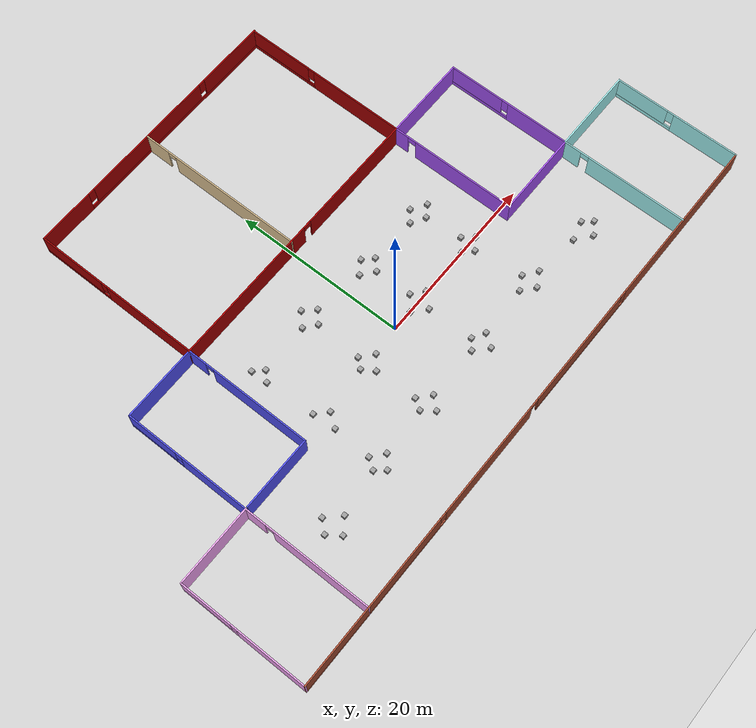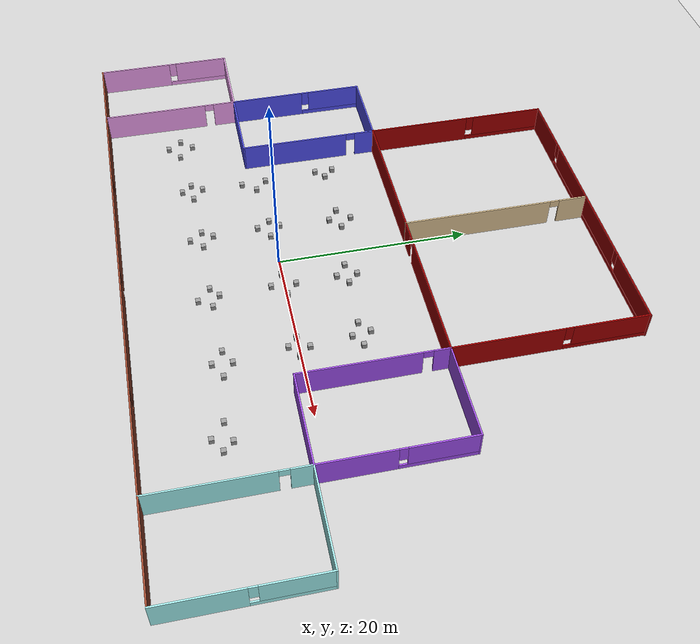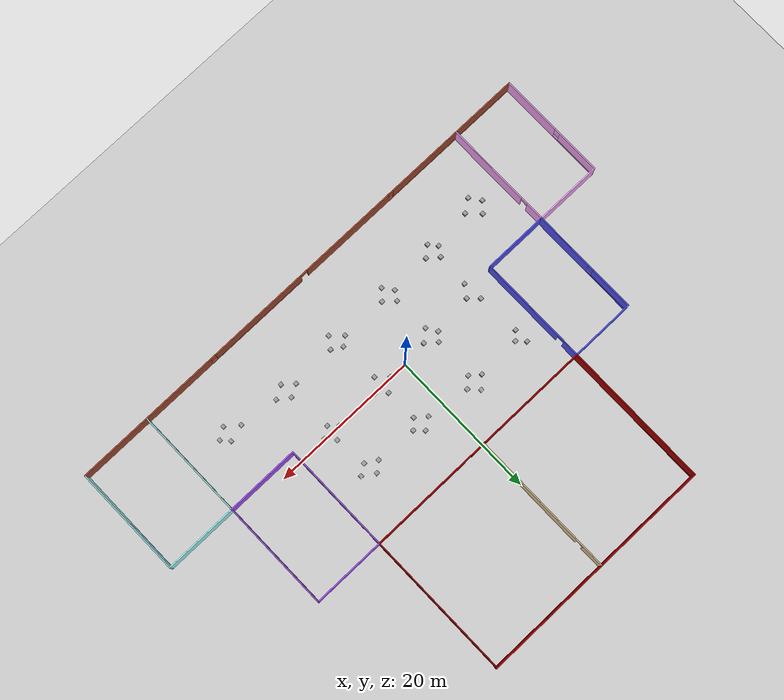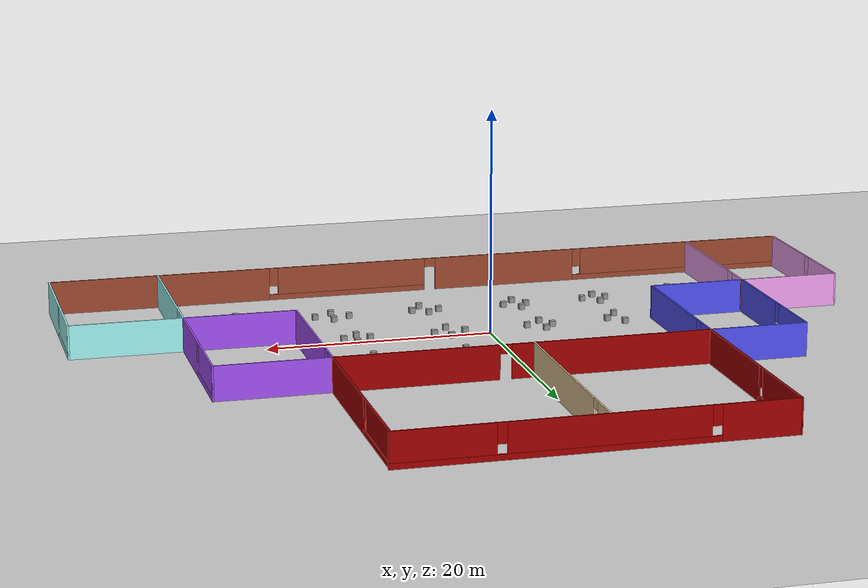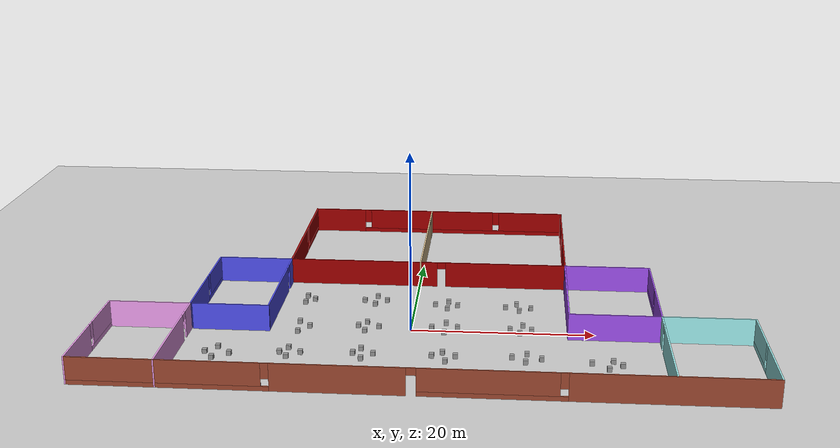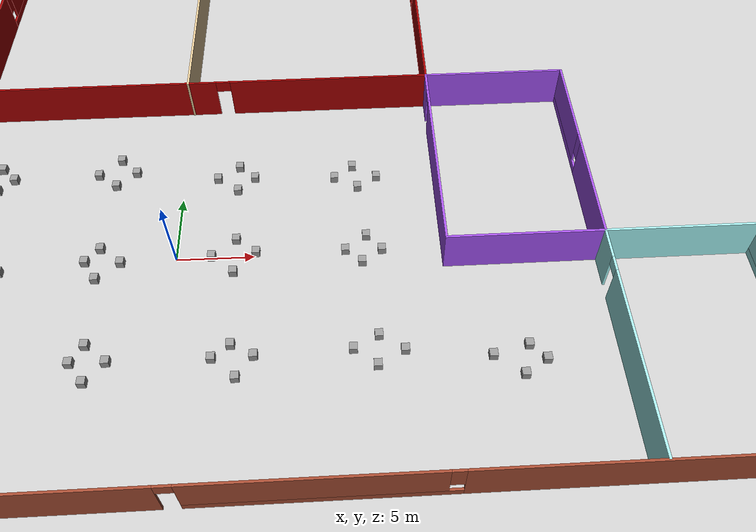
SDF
<sdf version="1.6">
 <world name="default">
  <plugin name="welcome" filename="libwelcome.so"/>
  <light name="sun" type="directional">
   <pose>0 0 10 0 -0 0</pose>
   <diffuse>0.8 0.8 0.8 1</diffuse>
   <specular>0.2 0.2 0.2 1</specular>
   <attenuation>
    <range>1000</range>
    <constant>0.9</constant>
    <linear>0.01</linear>
    <quadratic>0.001</quadratic>
   </attenuation>
   <direction>-0.5 0.1 -0.9</direction>
  </light>
  <model name="ground_plane">
   <static>1</static>
   <link name="link">
    <collision name="collision">
     <geometry><plane><normal>0 0 1</normal><size>100 100</size></plane></geometry>
     <surface>
      <contact><collide_bitmask>65535</collide_bitmask></contact>
      <friction><ode><mu>100</mu><mu2>50</mu2></ode></friction>
     </surface>
    </collision>
    <visual name="visual">
     <cast_shadows>0</cast_shadows>
     <geometry><plane><normal>0 0 1</normal><size>100 100</size></plane></geometry>
     <material>
      <script><uri>file://media/materials/scripts/gazebo.material</uri><name>Gazebo/Grey</name></script>
     </material>
    </visual>
   </link>
  </model>
  <gravity>0 0 -9.8</gravity>
  <magnetic_field>6e-06 2.3e-05 -4.2e-05</magnetic_field>
  <atmosphere type="adiabatic"/>
  <physics name="default_physics" default="0" type="ode">
   <max_step_size>0.001</max_step_size>
   <real_time_factor>1</real_time_factor>
   <real_time_update_rate>1000</real_time_update_rate>
  </physics>
  <scene><ambient>0.4 0.4 0.4 1</ambient><background>0.7 0.7 0.7 1</background><shadows>1</shadows></scene>
  <audio><device>default</device></audio>
  <spherical_coordinates>
   <surface_model>EARTH_WGS84</surface_model>
   <latitude_deg>0</latitude_deg>
   <longitude_deg>0</longitude_deg>
   <elevation>0</elevation>
   <heading_deg>0</heading_deg>
  </spherical_coordinates>
  <model name="myworld">
   <pose>1.87282 8.5844 0 0 -0 0</pose>
   <link name="Wall_13">
    <pose>1e-06 -24.775 0 0 -0 3.14159</pose>
    <visual name="Wall_13_Visual_0">
     <pose>-24.8847 0 1.5 0 -0 0</pose>
     <geometry><box><size>20.2306 0.15 3</size></box></geometry>
     <material>
      <script><uri>file://media/materials/scripts/gazebo.material</uri><name>Gazebo/Bricks</name></script>
      <ambient>1 1 1 1</ambient>
     </material>
     <meta><layer>0</layer></meta>
    </visual>
    <collision name="Wall_13_Collision_0">
     <geometry><box><size>20.2306 0.15 3</size></box></geometry>
     <pose>-24.8847 0 1.5 0 -0 0</pose>
    </collision>
    <visual name="Wall_13_Visual_1">
     <pose>7.72446 0 1.5 0 -0 0</pose>
     <geometry><box><size>13.4735 0.15 3</size></box></geometry>
     <material>
      <script><uri>file://media/materials/scripts/gazebo.material</uri><name>Gazebo/Bricks</name></script>
      <ambient>1 1 1 1</ambient>
     </material>
     <meta><layer>0</layer></meta>
    </visual>
    <collision name="Wall_13_Collision_1">
     <geometry><box><size>13.4735 0.15 3</size></box></geometry>
     <pose>7.72446 0 1.5 0 -0 0</pose>
    </collision>
    <visual name="Wall_13_Visual_2">
     <pose>-7.39085 0 0.25 0 -0 0</pose>
     <geometry><box><size>14.7571 0.15 0.5</size></box></geometry>
     <material>
      <script><uri>file://media/materials/scripts/gazebo.material</uri><name>Gazebo/Bricks</name></script>
      <ambient>1 1 1 1</ambient>
     </material>
     <meta><layer>0</layer></meta>
    </visual>
    <collision name="Wall_13_Collision_2">
     <geometry><box><size>14.7571 0.15 0.5</size></box></geometry>
     <pose>-7.39085 0 0.25 0 -0 0</pose>
    </collision>
    <visual name="Wall_13_Visual_3">
     <pose>24.7306 0 0.25 0 -0 0</pose>
     <geometry><box><size>20.5388 0.15 0.5</size></box></geometry>
     <material>
      <script><uri>file://media/materials/scripts/gazebo.material</uri><name>Gazebo/Bricks</name></script>
      <ambient>1 1 1 1</ambient>
     </material>
     <meta><layer>0</layer></meta>
    </visual>
    <collision name="Wall_13_Collision_3">
     <geometry><box><size>20.5388 0.15 0.5</size></box></geometry>
     <pose>24.7306 0 0.25 0 -0 0</pose>
    </collision>
    <visual name="Wall_13_Visual_5">
     <pose>-6.99085 0 1.75 0 -0 0</pose>
     <geometry><box><size>13.9571 0.15 2.5</size></box></geometry>
     <material>
      <script><uri>file://media/materials/scripts/gazebo.material</uri><name>Gazebo/Bricks</name></script>
      <ambient>1 1 1 1</ambient>
     </material>
     <meta><layer>0</layer></meta>
    </visual>
    <collision name="Wall_13_Collision_5">
     <geometry><box><size>13.9571 0.15 2.5</size></box></geometry>
     <pose>-6.99085 0 1.75 0 -0 0</pose>
    </collision>
    <visual name="Wall_13_Visual_6">
     <pose>-6.99085 0 1.75 0 -0 0</pose>
     <geometry><box><size>13.9571 0.15 2.5</size></box></geometry>
     <material>
      <script><uri>file://media/materials/scripts/gazebo.material</uri><name>Gazebo/Bricks</name></script>
      <ambient>1 1 1 1</ambient>
     </material>
     <meta><layer>0</layer></meta>
    </visual>
    <collision name="Wall_13_Collision_6">
     <geometry><box><size>13.9571 0.15 2.5</size></box></geometry>
     <pose>-6.99085 0 1.75 0 -0 0</pose>
    </collision>
    <visual name="Wall_13_Visual_7">
     <pose>25.1306 0 1.75 0 -0 0</pose>
     <geometry><box><size>19.7388 0.15 2.5</size></box></geometry>
     <material>
      <script><uri>file://media/materials/scripts/gazebo.material</uri><name>Gazebo/Bricks</name></script>
      <ambient>1 1 1 1</ambient>
     </material>
     <meta><layer>0</layer></meta>
    </visual>
    <collision name="Wall_13_Collision_7">
     <geometry><box><size>19.7388 0.15 2.5</size></box></geometry>
     <pose>25.1306 0 1.75 0 -0 0</pose>
    </collision>
    <visual name="Wall_13_Visual_8">
     <pose>-14.3694 0 2.15 0 -0 0</pose>
     <geometry><box><size>0.8 0.15 1.7</size></box></geometry>
     <material>
      <script><uri>file://media/materials/scripts/gazebo.material</uri><name>Gazebo/Bricks</name></script>
      <ambient>1 1 1 1</ambient>
     </material>
     <meta><layer>0</layer></meta>
    </visual>
    <collision name="Wall_13_Collision_8">
     <geometry><box><size>0.8 0.15 1.7</size></box></geometry>
     <pose>-14.3694 0 2.15 0 -0 0</pose>
    </collision>
    <visual name="Wall_13_Visual_9">
     <pose>14.8612 0 2.15 0 -0 0</pose>
     <geometry><box><size>0.8 0.15 1.7</size></box></geometry>
     <material>
      <script><uri>file://media/materials/scripts/gazebo.material</uri><name>Gazebo/Bricks</name></script>
      <ambient>1 1 1 1</ambient>
     </material>
     <meta><layer>0</layer></meta>
    </visual>
    <collision name="Wall_13_Collision_9">
     <geometry><box><size>0.8 0.15 1.7</size></box></geometry>
     <pose>14.8612 0 2.15 0 -0 0</pose>
    </collision>
    <visual name="Wall_13_Visual_10">
     <pose>0.487698 0 2.6 0 -0 0</pose>
     <geometry><box><size>1 0.15 0.8</size></box></geometry>
     <material>
      <script><uri>file://media/materials/scripts/gazebo.material</uri><name>Gazebo/Bricks</name></script>
      <ambient>1 1 1 1</ambient>
     </material>
     <meta><layer>0</layer></meta>
    </visual>
    <collision name="Wall_13_Collision_10">
     <geometry><box><size>1 0.15 0.8</size></box></geometry>
     <pose>0.487698 0 2.6 0 -0 0</pose>
    </collision>
    <visual name="Wall_13_Visual_11">
     <pose>0.487698 0 2.6 0 -0 0</pose>
     <geometry><box><size>1 0.15 0.8</size></box></geometry>
     <material>
      <script><uri>file://media/materials/scripts/gazebo.material</uri><name>Gazebo/Bricks</name></script>
      <ambient>1 1 1 1</ambient>
     </material>
     <meta><layer>0</layer></meta>
    </visual>
    <collision name="Wall_13_Collision_11">
     <geometry><box><size>1 0.15 0.8</size></box></geometry>
     <pose>0.487698 0 2.6 0 -0 0</pose>
    </collision>
   </link>
   <link name="Wall_14">
    <pose>-34.925 -17.35 0 0 -0 1.5708</pose>
    <visual name="Wall_14_Visual_0">
     <pose>-3.43526 0 1.5 0 -0 0</pose>
     <geometry><box><size>8.12947 0.15 3</size></box></geometry>
     <material>
      <script><uri>file://media/materials/scripts/gazebo.material</uri><name>Gazebo/Grey</name></script>
      <ambient>1 0.666667 1 1</ambient>
     </material>
     <meta><layer>0</layer></meta>
    </visual>
    <collision name="Wall_14_Collision_0">
     <geometry><box><size>8.12947 0.15 3</size></box></geometry>
     <pose>-3.43526 0 1.5 0 -0 0</pose>
    </collision>
    <visual name="Wall_14_Visual_1">
     <pose>4.06474 0 0.25 0 -0 0</pose>
     <geometry><box><size>6.87052 0.15 0.5</size></box></geometry>
     <material>
      <script><uri>file://media/materials/scripts/gazebo.material</uri><name>Gazebo/Grey</name></script>
      <ambient>1 0.666667 1 1</ambient>
     </material>
     <meta><layer>0</layer></meta>
    </visual>
    <collision name="Wall_14_Collision_1">
     <geometry><box><size>6.87052 0.15 0.5</size></box></geometry>
     <pose>4.06474 0 0.25 0 -0 0</pose>
    </collision>
    <visual name="Wall_14_Visual_2">
     <pose>4.46474 0 1.75 0 -0 0</pose>
     <geometry><box><size>6.07052 0.15 2.5</size></box></geometry>
     <material>
      <script><uri>file://media/materials/scripts/gazebo.material</uri><name>Gazebo/Grey</name></script>
      <ambient>1 0.666667 1 1</ambient>
     </material>
     <meta><layer>0</layer></meta>
    </visual>
    <collision name="Wall_14_Collision_2">
     <geometry><box><size>6.07052 0.15 2.5</size></box></geometry>
     <pose>4.46474 0 1.75 0 -0 0</pose>
    </collision>
    <visual name="Wall_14_Visual_3">
     <pose>1.02947 0 2.15 0 -0 0</pose>
     <geometry><box><size>0.8 0.15 1.7</size></box></geometry>
     <material>
      <script><uri>file://media/materials/scripts/gazebo.material</uri><name>Gazebo/Grey</name></script>
      <ambient>1 0.666667 1 1</ambient>
     </material>
     <meta><layer>0</layer></meta>
    </visual>
    <collision name="Wall_14_Collision_3">
     <geometry><box><size>0.8 0.15 1.7</size></box></geometry>
     <pose>1.02947 0 2.15 0 -0 0</pose>
    </collision>
   </link>
   <link name="Wall_15">
    <collision name="Wall_15_Collision">
     <geometry><box><size>9.165 0.15 3</size></box></geometry>
     <pose>0 0 1.5 0 -0 0</pose>
    </collision>
    <visual name="Wall_15_Visual">
     <pose>0 0 1.5 0 -0 0</pose>
     <geometry><box><size>9.165 0.15 3</size></box></geometry>
     <material>
      <script><uri>file://media/materials/scripts/gazebo.material</uri><name>Gazebo/Grey</name></script>
      <ambient>1 0.666667 1 1</ambient>
     </material>
     <meta><layer>0</layer></meta>
    </visual>
    <pose>-30.4175 -9.925 0 0 -0 0</pose>
   </link>
   <link name="Wall_21">
    <pose>-25.91 -2.5 0 0 -0 1.5708</pose>
    <visual name="Wall_21_Visual_0">
     <pose>-3.41555 0 1.5 0 -0 0</pose>
     <geometry><box><size>8.16889 0.15 3</size></box></geometry>
     <material>
      <script><uri>file://media/materials/scripts/gazebo.material</uri><name>Gazebo/Grey</name></script>
      <ambient>0.333333 0.333333 1 1</ambient>
     </material>
     <meta><layer>0</layer></meta>
    </visual>
    <collision name="Wall_21_Collision_0">
     <geometry><box><size>8.16889 0.15 3</size></box></geometry>
     <pose>-3.41555 0 1.5 0 -0 0</pose>
    </collision>
    <visual name="Wall_21_Visual_1">
     <pose>4.08445 0 0.25 0 -0 0</pose>
     <geometry><box><size>6.83111 0.15 0.5</size></box></geometry>
     <material>
      <script><uri>file://media/materials/scripts/gazebo.material</uri><name>Gazebo/Grey</name></script>
      <ambient>0.333333 0.333333 1 1</ambient>
     </material>
     <meta><layer>0</layer></meta>
    </visual>
    <collision name="Wall_21_Collision_1">
     <geometry><box><size>6.83111 0.15 0.5</size></box></geometry>
     <pose>4.08445 0 0.25 0 -0 0</pose>
    </collision>
    <visual name="Wall_21_Visual_2">
     <pose>4.48445 0 1.75 0 -0 0</pose>
     <geometry><box><size>6.03111 0.15 2.5</size></box></geometry>
     <material>
      <script><uri>file://media/materials/scripts/gazebo.material</uri><name>Gazebo/Grey</name></script>
      <ambient>0.333333 0.333333 1 1</ambient>
     </material>
     <meta><layer>0</layer></meta>
    </visual>
    <collision name="Wall_21_Collision_2">
     <geometry><box><size>6.03111 0.15 2.5</size></box></geometry>
     <pose>4.48445 0 1.75 0 -0 0</pose>
    </collision>
    <visual name="Wall_21_Visual_3">
     <pose>1.06889 0 2.15 0 -0 0</pose>
     <geometry><box><size>0.8 0.15 1.7</size></box></geometry>
     <material>
      <script><uri>file://media/materials/scripts/gazebo.material</uri><name>Gazebo/Grey</name></script>
      <ambient>0.333333 0.333333 1 1</ambient>
     </material>
     <meta><layer>0</layer></meta>
    </visual>
    <collision name="Wall_21_Collision_3">
     <geometry><box><size>0.8 0.15 1.7</size></box></geometry>
     <pose>1.06889 0 2.15 0 -0 0</pose>
    </collision>
   </link>
   <link name="Wall_22">
    <collision name="Wall_22_Collision">
     <geometry><box><size>8.786 0.15 3</size></box></geometry>
     <pose>0 0 1.5 0 -0 0</pose>
    </collision>
    <visual name="Wall_22_Visual">
     <pose>0 0 1.5 0 -0 0</pose>
     <geometry><box><size>8.786 0.15 3</size></box></geometry>
     <material>
      <script><uri>file://media/materials/scripts/gazebo.material</uri><name>Gazebo/Grey</name></script>
      <ambient>0.333333 0.333333 1 1</ambient>
     </material>
     <meta><layer>0</layer></meta>
    </visual>
    <pose>-21.592 4.925 0 0 -0 0</pose>
   </link>
   <link name="Wall_24">
    <pose>-17.274 14.85 0 0 -0 1.5708</pose>
    <visual name="Wall_24_Visual_0">
     <pose>-4.4064 0 1.5 0 -0 0</pose>
     <geometry><box><size>11.1872 0.15 3</size></box></geometry>
     <material>
      <script><uri>file://media/materials/scripts/gazebo.material</uri><name>Gazebo/Grey</name></script>
      <ambient>0.666667 0 0 1</ambient>
     </material>
     <meta><layer>0</layer></meta>
    </visual>
    <collision name="Wall_24_Collision_0">
     <geometry><box><size>11.1872 0.15 3</size></box></geometry>
     <pose>-4.4064 0 1.5 0 -0 0</pose>
    </collision>
    <visual name="Wall_24_Visual_1">
     <pose>5.5936 0 0.25 0 -0 0</pose>
     <geometry><box><size>8.8128 0.15 0.5</size></box></geometry>
     <material>
      <script><uri>file://media/materials/scripts/gazebo.material</uri><name>Gazebo/Grey</name></script>
      <ambient>0.666667 0 0 1</ambient>
     </material>
     <meta><layer>0</layer></meta>
    </visual>
    <collision name="Wall_24_Collision_1">
     <geometry><box><size>8.8128 0.15 0.5</size></box></geometry>
     <pose>5.5936 0 0.25 0 -0 0</pose>
    </collision>
    <visual name="Wall_24_Visual_2">
     <pose>5.9936 0 1.75 0 -0 0</pose>
     <geometry><box><size>8.0128 0.15 2.5</size></box></geometry>
     <material>
      <script><uri>file://media/materials/scripts/gazebo.material</uri><name>Gazebo/Grey</name></script>
      <ambient>0.666667 0 0 1</ambient>
     </material>
     <meta><layer>0</layer></meta>
    </visual>
    <collision name="Wall_24_Collision_2">
     <geometry><box><size>8.0128 0.15 2.5</size></box></geometry>
     <pose>5.9936 0 1.75 0 -0 0</pose>
    </collision>
    <visual name="Wall_24_Visual_3">
     <pose>1.5872 0 2.15 0 -0 0</pose>
     <geometry><box><size>0.8 0.15 1.7</size></box></geometry>
     <material>
      <script><uri>file://media/materials/scripts/gazebo.material</uri><name>Gazebo/Grey</name></script>
      <ambient>0.666667 0 0 1</ambient>
     </material>
     <meta><layer>0</layer></meta>
    </visual>
    <collision name="Wall_24_Collision_3">
     <geometry><box><size>0.8 0.15 1.7</size></box></geometry>
     <pose>1.5872 0 2.15 0 -0 0</pose>
    </collision>
   </link>
   <link name="Wall_25">
    <pose>-0.974 24.775 0 0 -0 0</pose>
    <visual name="Wall_25_Visual_0">
     <pose>-13.0895 0 1.5 0 -0 0</pose>
     <geometry><box><size>6.57101 0.15 3</size></box></geometry>
     <material>
      <script><uri>file://media/materials/scripts/gazebo.material</uri><name>Gazebo/Grey</name></script>
      <ambient>0.666667 0 0 1</ambient>
     </material>
     <meta><layer>0</layer></meta>
    </visual>
    <collision name="Wall_25_Collision_0">
     <geometry><box><size>6.57101 0.15 3</size></box></geometry>
     <pose>-13.0895 0 1.5 0 -0 0</pose>
    </collision>
    <visual name="Wall_25_Visual_1">
     <pose>3.2855 0 0.25 0 -0 0</pose>
     <geometry><box><size>26.179 0.15 0.5</size></box></geometry>
     <material>
      <script><uri>file://media/materials/scripts/gazebo.material</uri><name>Gazebo/Grey</name></script>
      <ambient>0.666667 0 0 1</ambient>
     </material>
     <meta><layer>0</layer></meta>
    </visual>
    <collision name="Wall_25_Collision_1">
     <geometry><box><size>26.179 0.15 0.5</size></box></geometry>
     <pose>3.2855 0 0.25 0 -0 0</pose>
    </collision>
    <visual name="Wall_25_Visual_2">
     <pose>-0.885868 0 1.75 0 -0 0</pose>
     <geometry><box><size>16.2363 0.15 2.5</size></box></geometry>
     <material>
      <script><uri>file://media/materials/scripts/gazebo.material</uri><name>Gazebo/Grey</name></script>
      <ambient>0.666667 0 0 1</ambient>
     </material>
     <meta><layer>0</layer></meta>
    </visual>
    <collision name="Wall_25_Collision_2">
     <geometry><box><size>16.2363 0.15 2.5</size></box></geometry>
     <pose>-0.885868 0 1.75 0 -0 0</pose>
    </collision>
    <visual name="Wall_25_Visual_3">
     <pose>12.2036 0 1.75 0 -0 0</pose>
     <geometry><box><size>8.34274 0.15 2.5</size></box></geometry>
     <material>
      <script><uri>file://media/materials/scripts/gazebo.material</uri><name>Gazebo/Grey</name></script>
      <ambient>0.666667 0 0 1</ambient>
     </material>
     <meta><layer>0</layer></meta>
    </visual>
    <collision name="Wall_25_Collision_3">
     <geometry><box><size>8.34274 0.15 2.5</size></box></geometry>
     <pose>12.2036 0 1.75 0 -0 0</pose>
    </collision>
    <visual name="Wall_25_Visual_4">
     <pose>-9.40399 0 2.15 0 -0 0</pose>
     <geometry><box><size>0.8 0.15 1.7</size></box></geometry>
     <material>
      <script><uri>file://media/materials/scripts/gazebo.material</uri><name>Gazebo/Grey</name></script>
      <ambient>0.666667 0 0 1</ambient>
     </material>
     <meta><layer>0</layer></meta>
    </visual>
    <collision name="Wall_25_Collision_4">
     <geometry><box><size>0.8 0.15 1.7</size></box></geometry>
     <pose>-9.40399 0 2.15 0 -0 0</pose>
    </collision>
    <visual name="Wall_25_Visual_5">
     <pose>7.63226 0 2.15 0 -0 0</pose>
     <geometry><box><size>0.8 0.15 1.7</size></box></geometry>
     <material>
      <script><uri>file://media/materials/scripts/gazebo.material</uri><name>Gazebo/Grey</name></script>
      <ambient>0.666667 0 0 1</ambient>
     </material>
     <meta><layer>0</layer></meta>
    </visual>
    <collision name="Wall_25_Collision_5">
     <geometry><box><size>0.8 0.15 1.7</size></box></geometry>
     <pose>7.63226 0 2.15 0 -0 0</pose>
    </collision>
   </link>
   <link name="Wall_27">
    <pose>34.925 -17.35 0 0 -0 1.5708</pose>
    <visual name="Wall_27_Visual_0">
     <pose>-3.569 0 1.5 0 -0 0</pose>
     <geometry><box><size>7.862 0.15 3</size></box></geometry>
     <material>
      <script><uri>file://media/materials/scripts/gazebo.material</uri><name>Gazebo/Grey</name></script>
      <ambient>0.666667 1 1 1</ambient>
     </material>
     <meta><layer>0</layer></meta>
    </visual>
    <collision name="Wall_27_Collision_0">
     <geometry><box><size>7.862 0.15 3</size></box></geometry>
     <pose>-3.569 0 1.5 0 -0 0</pose>
    </collision>
    <visual name="Wall_27_Visual_1">
     <pose>3.931 0 0.25 0 -0 0</pose>
     <geometry><box><size>7.138 0.15 0.5</size></box></geometry>
     <material>
      <script><uri>file://media/materials/scripts/gazebo.material</uri><name>Gazebo/Grey</name></script>
      <ambient>0.666667 1 1 1</ambient>
     </material>
     <meta><layer>0</layer></meta>
    </visual>
    <collision name="Wall_27_Collision_1">
     <geometry><box><size>7.138 0.15 0.5</size></box></geometry>
     <pose>3.931 0 0.25 0 -0 0</pose>
    </collision>
    <visual name="Wall_27_Visual_2">
     <pose>4.331 0 1.75 0 -0 0</pose>
     <geometry><box><size>6.338 0.15 2.5</size></box></geometry>
     <material>
      <script><uri>file://media/materials/scripts/gazebo.material</uri><name>Gazebo/Grey</name></script>
      <ambient>0.666667 1 1 1</ambient>
     </material>
     <meta><layer>0</layer></meta>
    </visual>
    <collision name="Wall_27_Collision_2">
     <geometry><box><size>6.338 0.15 2.5</size></box></geometry>
     <pose>4.331 0 1.75 0 -0 0</pose>
    </collision>
    <visual name="Wall_27_Visual_3">
     <pose>0.762001 0 2.15 0 -0 0</pose>
     <geometry><box><size>0.8 0.15 1.7</size></box></geometry>
     <material>
      <script><uri>file://media/materials/scripts/gazebo.material</uri><name>Gazebo/Grey</name></script>
      <ambient>0.666667 1 1 1</ambient>
     </material>
     <meta><layer>0</layer></meta>
    </visual>
    <collision name="Wall_27_Collision_3">
     <geometry><box><size>0.8 0.15 1.7</size></box></geometry>
     <pose>0.762001 0 2.15 0 -0 0</pose>
    </collision>
   </link>
   <link name="Wall_28">
    <collision name="Wall_28_Collision">
     <geometry><box><size>9.997 0.15 3</size></box></geometry>
     <pose>0 0 1.5 0 -0 0</pose>
    </collision>
    <visual name="Wall_28_Visual">
     <pose>0 0 1.5 0 -0 0</pose>
     <geometry><box><size>9.997 0.15 3</size></box></geometry>
     <material>
      <script><uri>file://media/materials/scripts/gazebo.material</uri><name>Gazebo/Grey</name></script>
      <ambient>0.666667 1 1 1</ambient>
     </material>
     <meta><layer>0</layer></meta>
    </visual>
    <pose>30.0015 -9.925 0 0 -0 3.14159</pose>
   </link>
   <link name="Wall_31">
    <pose>25.078 -2.5 0 0 -0 1.5708</pose>
    <visual name="Wall_31_Visual_0">
     <pose>-3.72761 0 1.5 0 -0 0</pose>
     <geometry><box><size>7.54479 0.15 3</size></box></geometry>
     <material>
      <script><uri>file://media/materials/scripts/gazebo.material</uri><name>Gazebo/Grey</name></script>
      <ambient>0.666667 0.333333 1 1</ambient>
     </material>
     <meta><layer>0</layer></meta>
    </visual>
    <collision name="Wall_31_Collision_0">
     <geometry><box><size>7.54479 0.15 3</size></box></geometry>
     <pose>-3.72761 0 1.5 0 -0 0</pose>
    </collision>
    <visual name="Wall_31_Visual_1">
     <pose>3.77239 0 0.25 0 -0 0</pose>
     <geometry><box><size>7.45521 0.15 0.5</size></box></geometry>
     <material>
      <script><uri>file://media/materials/scripts/gazebo.material</uri><name>Gazebo/Grey</name></script>
      <ambient>0.666667 0.333333 1 1</ambient>
     </material>
     <meta><layer>0</layer></meta>
    </visual>
    <collision name="Wall_31_Collision_1">
     <geometry><box><size>7.45521 0.15 0.5</size></box></geometry>
     <pose>3.77239 0 0.25 0 -0 0</pose>
    </collision>
    <visual name="Wall_31_Visual_2">
     <pose>4.17239 0 1.75 0 -0 0</pose>
     <geometry><box><size>6.65521 0.15 2.5</size></box></geometry>
     <material>
      <script><uri>file://media/materials/scripts/gazebo.material</uri><name>Gazebo/Grey</name></script>
      <ambient>0.666667 0.333333 1 1</ambient>
     </material>
     <meta><layer>0</layer></meta>
    </visual>
    <collision name="Wall_31_Collision_2">
     <geometry><box><size>6.65521 0.15 2.5</size></box></geometry>
     <pose>4.17239 0 1.75 0 -0 0</pose>
    </collision>
    <visual name="Wall_31_Visual_3">
     <pose>0.444787 0 2.15 0 -0 0</pose>
     <geometry><box><size>0.8 0.15 1.7</size></box></geometry>
     <material>
      <script><uri>file://media/materials/scripts/gazebo.material</uri><name>Gazebo/Grey</name></script>
      <ambient>0.666667 0.333333 1 1</ambient>
     </material>
     <meta><layer>0</layer></meta>
    </visual>
    <collision name="Wall_31_Collision_3">
     <geometry><box><size>0.8 0.15 1.7</size></box></geometry>
     <pose>0.444787 0 2.15 0 -0 0</pose>
    </collision>
   </link>
   <link name="Wall_32">
    <collision name="Wall_32_Collision">
     <geometry><box><size>9.987 0.15 3</size></box></geometry>
     <pose>0 0 1.5 0 -0 0</pose>
    </collision>
    <visual name="Wall_32_Visual">
     <pose>0 0 1.5 0 -0 0</pose>
     <geometry><box><size>9.987 0.15 3</size></box></geometry>
     <material>
      <script><uri>file://media/materials/scripts/gazebo.material</uri><name>Gazebo/Grey</name></script>
      <ambient>0.666667 0.333333 1 1</ambient>
     </material>
     <meta><layer>0</layer></meta>
    </visual>
    <pose>20.1595 4.925 0 0 -0 3.14159</pose>
   </link>
   <link name="Wall_34">
    <pose>15.241 14.849 0 0 -0 1.5708</pose>
    <visual name="Wall_34_Visual_0">
     <pose>-4.30287 0 1.5 0 -0 0</pose>
     <geometry><box><size>11.3923 0.15 3</size></box></geometry>
     <material>
      <script><uri>file://media/materials/scripts/gazebo.material</uri><name>Gazebo/Grey</name></script>
      <ambient>0.666667 0 0 1</ambient>
     </material>
     <meta><layer>0</layer></meta>
    </visual>
    <collision name="Wall_34_Collision_0">
     <geometry><box><size>11.3923 0.15 3</size></box></geometry>
     <pose>-4.30287 0 1.5 0 -0 0</pose>
    </collision>
    <visual name="Wall_34_Visual_1">
     <pose>5.69613 0 0.25 0 -0 0</pose>
     <geometry><box><size>8.60573 0.15 0.5</size></box></geometry>
     <material>
      <script><uri>file://media/materials/scripts/gazebo.material</uri><name>Gazebo/Grey</name></script>
      <ambient>0.666667 0 0 1</ambient>
     </material>
     <meta><layer>0</layer></meta>
    </visual>
    <collision name="Wall_34_Collision_1">
     <geometry><box><size>8.60573 0.15 0.5</size></box></geometry>
     <pose>5.69613 0 0.25 0 -0 0</pose>
    </collision>
    <visual name="Wall_34_Visual_2">
     <pose>6.09613 0 1.75 0 -0 0</pose>
     <geometry><box><size>7.80573 0.15 2.5</size></box></geometry>
     <material>
      <script><uri>file://media/materials/scripts/gazebo.material</uri><name>Gazebo/Grey</name></script>
      <ambient>0.666667 0 0 1</ambient>
     </material>
     <meta><layer>0</layer></meta>
    </visual>
    <collision name="Wall_34_Collision_2">
     <geometry><box><size>7.80573 0.15 2.5</size></box></geometry>
     <pose>6.09613 0 1.75 0 -0 0</pose>
    </collision>
    <visual name="Wall_34_Visual_3">
     <pose>1.79327 0 2.15 0 -0 0</pose>
     <geometry><box><size>0.8 0.15 1.7</size></box></geometry>
     <material>
      <script><uri>file://media/materials/scripts/gazebo.material</uri><name>Gazebo/Grey</name></script>
      <ambient>0.666667 0 0 1</ambient>
     </material>
     <meta><layer>0</layer></meta>
    </visual>
    <collision name="Wall_34_Collision_3">
     <geometry><box><size>0.8 0.15 1.7</size></box></geometry>
     <pose>1.79327 0 2.15 0 -0 0</pose>
    </collision>
   </link>
   <link name="Wall_37">
    <pose>-25.91 -17.35 0 0 0 -1.5708</pose>
    <visual name="Wall_37_Visual_0">
     <pose>-6.24162 0 1.5 0 -0 0</pose>
     <geometry><box><size>2.51676 0.15 3</size></box></geometry>
     <material>
      <script><uri>file://media/materials/scripts/gazebo.material</uri><name>Gazebo/Grey</name></script>
      <ambient>1 0.666667 1 1</ambient>
     </material>
     <meta><layer>0</layer></meta>
    </visual>
    <collision name="Wall_37_Collision_0">
     <geometry><box><size>2.51676 0.15 3</size></box></geometry>
     <pose>-6.24162 0 1.5 0 -0 0</pose>
    </collision>
    <visual name="Wall_37_Visual_1">
     <pose>1.75838 0 1.5 0 -0 0</pose>
     <geometry><box><size>11.4832 0.15 3</size></box></geometry>
     <material>
      <script><uri>file://media/materials/scripts/gazebo.material</uri><name>Gazebo/Grey</name></script>
      <ambient>1 0.666667 1 1</ambient>
     </material>
     <meta><layer>0</layer></meta>
    </visual>
    <collision name="Wall_37_Collision_1">
     <geometry><box><size>11.4832 0.15 3</size></box></geometry>
     <pose>1.75838 0 1.5 0 -0 0</pose>
    </collision>
    <visual name="Wall_37_Visual_3">
     <pose>-4.48324 0 2.6 0 -0 0</pose>
     <geometry><box><size>1 0.15 0.8</size></box></geometry>
     <material>
      <script><uri>file://media/materials/scripts/gazebo.material</uri><name>Gazebo/Grey</name></script>
      <ambient>1 0.666667 1 1</ambient>
     </material>
     <meta><layer>0</layer></meta>
    </visual>
    <collision name="Wall_37_Collision_3">
     <geometry><box><size>1 0.15 0.8</size></box></geometry>
     <pose>-4.48324 0 2.6 0 -0 0</pose>
    </collision>
   </link>
   <link name="Wall_40">
    <pose>-17.274 -2.5 0 0 0 -1.5708</pose>
    <visual name="Wall_40_Visual_0">
     <pose>-6.38157 0 1.5 0 -0 0</pose>
     <geometry><box><size>2.23685 0.15 3</size></box></geometry>
     <material>
      <script><uri>file://media/materials/scripts/gazebo.material</uri><name>Gazebo/Grey</name></script>
      <ambient>0.333333 0.333333 1 1</ambient>
     </material>
     <meta><layer>0</layer></meta>
    </visual>
    <collision name="Wall_40_Collision_0">
     <geometry><box><size>2.23685 0.15 3</size></box></geometry>
     <pose>-6.38157 0 1.5 0 -0 0</pose>
    </collision>
    <visual name="Wall_40_Visual_1">
     <pose>1.61843 0 1.5 0 -0 0</pose>
     <geometry><box><size>11.7631 0.15 3</size></box></geometry>
     <material>
      <script><uri>file://media/materials/scripts/gazebo.material</uri><name>Gazebo/Grey</name></script>
      <ambient>0.333333 0.333333 1 1</ambient>
     </material>
     <meta><layer>0</layer></meta>
    </visual>
    <collision name="Wall_40_Collision_1">
     <geometry><box><size>11.7631 0.15 3</size></box></geometry>
     <pose>1.61843 0 1.5 0 -0 0</pose>
    </collision>
    <visual name="Wall_40_Visual_3">
     <pose>-4.76315 0 2.6 0 -0 0</pose>
     <geometry><box><size>1 0.15 0.8</size></box></geometry>
     <material>
      <script><uri>file://media/materials/scripts/gazebo.material</uri><name>Gazebo/Grey</name></script>
      <ambient>0.333333 0.333333 1 1</ambient>
     </material>
     <meta><layer>0</layer></meta>
    </visual>
    <collision name="Wall_40_Collision_3">
     <geometry><box><size>1 0.15 0.8</size></box></geometry>
     <pose>-4.76315 0 2.6 0 -0 0</pose>
    </collision>
   </link>
   <link name="Wall_41">
    <collision name="Wall_41_Collision">
     <geometry><box><size>8.5 0.15 3</size></box></geometry>
     <pose>0 0 1.5 0 -0 0</pose>
    </collision>
    <visual name="Wall_41_Visual">
     <pose>0 0 1.5 0 -0 0</pose>
     <geometry><box><size>8.5 0.15 3</size></box></geometry>
     <material>
      <script><uri>file://media/materials/scripts/gazebo.material</uri><name>Gazebo/Grey</name></script>
      <ambient>0.333333 0.333333 1 1</ambient>
     </material>
     <meta><layer>0</layer></meta>
    </visual>
    <pose>-21.449 -9.925 0 0 -0 3.14159</pose>
   </link>
   <link name="Wall_43">
    <pose>-1.059 4.925 0 0 -0 0</pose>
    <visual name="Wall_43_Visual_0">
     <pose>-7.58275 0 1.5 0 -0 0</pose>
     <geometry><box><size>17.5845 0.15 3</size></box></geometry>
     <material>
      <script><uri>file://media/materials/scripts/gazebo.material</uri><name>Gazebo/Grey</name></script>
      <ambient>0.666667 0 0 1</ambient>
     </material>
     <meta><layer>0</layer></meta>
    </visual>
    <collision name="Wall_43_Collision_0">
     <geometry><box><size>17.5845 0.15 3</size></box></geometry>
     <pose>-7.58275 0 1.5 0 -0 0</pose>
    </collision>
    <visual name="Wall_43_Visual_1">
     <pose>9.29224 0 1.5 0 -0 0</pose>
     <geometry><box><size>14.1655 0.15 3</size></box></geometry>
     <material>
      <script><uri>file://media/materials/scripts/gazebo.material</uri><name>Gazebo/Grey</name></script>
      <ambient>0.666667 0 0 1</ambient>
     </material>
     <meta><layer>0</layer></meta>
    </visual>
    <collision name="Wall_43_Collision_1">
     <geometry><box><size>14.1655 0.15 3</size></box></geometry>
     <pose>9.29224 0 1.5 0 -0 0</pose>
    </collision>
    <visual name="Wall_43_Visual_3">
     <pose>1.70949 0 2.6 0 -0 0</pose>
     <geometry><box><size>1 0.15 0.8</size></box></geometry>
     <material>
      <script><uri>file://media/materials/scripts/gazebo.material</uri><name>Gazebo/Grey</name></script>
      <ambient>0.666667 0 0 1</ambient>
     </material>
     <meta><layer>0</layer></meta>
    </visual>
    <collision name="Wall_43_Collision_3">
     <geometry><box><size>1 0.15 0.8</size></box></geometry>
     <pose>1.70949 0 2.6 0 -0 0</pose>
    </collision>
   </link>
   <link name="Wall_47">
    <pose>-1.828 14.819 0 0 0 -1.5708</pose>
    <visual name="Wall_47_Visual_0">
     <pose>-8.46017 0 1.5 0 -0 0</pose>
     <geometry><box><size>3.07967 0.15 3</size></box></geometry>
     <material>
      <script><uri>file://media/materials/scripts/gazebo.material</uri><name>Gazebo/Grey</name></script>
      <ambient>0.921569 0.807843 0.615686 1</ambient>
     </material>
     <meta><layer>0</layer></meta>
    </visual>
    <collision name="Wall_47_Collision_0">
     <geometry><box><size>3.07967 0.15 3</size></box></geometry>
     <pose>-8.46017 0 1.5 0 -0 0</pose>
    </collision>
    <visual name="Wall_47_Visual_1">
     <pose>2.03983 0 1.5 0 -0 0</pose>
     <geometry><box><size>15.9203 0.15 3</size></box></geometry>
     <material>
      <script><uri>file://media/materials/scripts/gazebo.material</uri><name>Gazebo/Grey</name></script>
      <ambient>0.921569 0.807843 0.615686 1</ambient>
     </material>
     <meta><layer>0</layer></meta>
    </visual>
    <collision name="Wall_47_Collision_1">
     <geometry><box><size>15.9203 0.15 3</size></box></geometry>
     <pose>2.03983 0 1.5 0 -0 0</pose>
    </collision>
    <visual name="Wall_47_Visual_3">
     <pose>-6.42033 0 2.61 0 -0 0</pose>
     <geometry><box><size>1 0.15 0.78</size></box></geometry>
     <material>
      <script><uri>file://media/materials/scripts/gazebo.material</uri><name>Gazebo/Grey</name></script>
      <ambient>0.921569 0.807843 0.615686 1</ambient>
     </material>
     <meta><layer>0</layer></meta>
    </visual>
    <collision name="Wall_47_Collision_3">
     <geometry><box><size>1 0.15 0.78</size></box></geometry>
     <pose>-6.42033 0 2.61 0 -0 0</pose>
    </collision>
   </link>
   <link name="Wall_49">
    <pose>25.078 -17.35 0 0 0 -1.5708</pose>
    <visual name="Wall_49_Visual_0">
     <pose>-6.44514 0 1.5 0 -0 0</pose>
     <geometry><box><size>2.10971 0.15 3</size></box></geometry>
     <material>
      <script><uri>file://media/materials/scripts/gazebo.material</uri><name>Gazebo/Grey</name></script>
      <ambient>0.666667 1 1 1</ambient>
     </material>
     <meta><layer>0</layer></meta>
    </visual>
    <collision name="Wall_49_Collision_0">
     <geometry><box><size>2.10971 0.15 3</size></box></geometry>
     <pose>-6.44514 0 1.5 0 -0 0</pose>
    </collision>
    <visual name="Wall_49_Visual_1">
     <pose>1.55486 0 1.5 0 -0 0</pose>
     <geometry><box><size>11.8903 0.15 3</size></box></geometry>
     <material>
      <script><uri>file://media/materials/scripts/gazebo.material</uri><name>Gazebo/Grey</name></script>
      <ambient>0.666667 1 1 1</ambient>
     </material>
     <meta><layer>0</layer></meta>
    </visual>
    <collision name="Wall_49_Collision_1">
     <geometry><box><size>11.8903 0.15 3</size></box></geometry>
     <pose>1.55486 0 1.5 0 -0 0</pose>
    </collision>
    <visual name="Wall_49_Visual_3">
     <pose>-4.89029 0 2.6 0 -0 0</pose>
     <geometry><box><size>1 0.15 0.8</size></box></geometry>
     <material>
      <script><uri>file://media/materials/scripts/gazebo.material</uri><name>Gazebo/Grey</name></script>
      <ambient>0.666667 1 1 1</ambient>
     </material>
     <meta><layer>0</layer></meta>
    </visual>
    <collision name="Wall_49_Collision_3">
     <geometry><box><size>1 0.15 0.8</size></box></geometry>
     <pose>-4.89029 0 2.6 0 -0 0</pose>
    </collision>
   </link>
   <link name="Wall_51">
    <pose>15.241 -2.5 0 0 0 -1.5708</pose>
    <visual name="Wall_51_Visual_0">
     <pose>-6.63801 0 1.5 0 -0 0</pose>
     <geometry><box><size>1.72398 0.15 3</size></box></geometry>
     <material>
      <script><uri>file://media/materials/scripts/gazebo.material</uri><name>Gazebo/Grey</name></script>
      <ambient>0.666667 0.333333 1 1</ambient>
     </material>
     <meta><layer>0</layer></meta>
    </visual>
    <collision name="Wall_51_Collision_0">
     <geometry><box><size>1.72398 0.15 3</size></box></geometry>
     <pose>-6.63801 0 1.5 0 -0 0</pose>
    </collision>
    <visual name="Wall_51_Visual_1">
     <pose>1.36199 0 1.5 0 -0 0</pose>
     <geometry><box><size>12.276 0.15 3</size></box></geometry>
     <material>
      <script><uri>file://media/materials/scripts/gazebo.material</uri><name>Gazebo/Grey</name></script>
      <ambient>0.666667 0.333333 1 1</ambient>
     </material>
     <meta><layer>0</layer></meta>
    </visual>
    <collision name="Wall_51_Collision_1">
     <geometry><box><size>12.276 0.15 3</size></box></geometry>
     <pose>1.36199 0 1.5 0 -0 0</pose>
    </collision>
    <visual name="Wall_51_Visual_3">
     <pose>-5.27602 0 2.6 0 -0 0</pose>
     <geometry><box><size>1 0.15 0.8</size></box></geometry>
     <material>
      <script><uri>file://media/materials/scripts/gazebo.material</uri><name>Gazebo/Grey</name></script>
      <ambient>0.666667 0.333333 1 1</ambient>
     </material>
     <meta><layer>0</layer></meta>
    </visual>
    <collision name="Wall_51_Collision_3">
     <geometry><box><size>1 0.15 0.8</size></box></geometry>
     <pose>-5.27602 0 2.6 0 -0 0</pose>
    </collision>
   </link>
   <link name="Wall_52">
    <collision name="Wall_52_Collision">
     <geometry><box><size>9.987 0.15 3</size></box></geometry>
     <pose>0 0 1.5 0 -0 0</pose>
    </collision>
    <visual name="Wall_52_Visual">
     <pose>0 0 1.5 0 -0 0</pose>
     <geometry><box><size>9.987 0.15 3</size></box></geometry>
     <material>
      <script><uri>file://media/materials/scripts/gazebo.material</uri><name>Gazebo/Grey</name></script>
      <ambient>0.666667 0.333333 1 1</ambient>
     </material>
     <meta><layer>0</layer></meta>
    </visual>
    <pose>20.1595 -9.925 0 0 -0 0</pose>
   </link>
   <static>1</static>
  </model>
  <model name="Untitled">
   <link name="link_0">
    <inertial>
     <mass>1</mass>
     <inertia>
      <ixx>0.166667</ixx>
      <ixy>0</ixy>
      <ixz>0</ixz>
      <iyy>0.166667</iyy>
      <iyz>0</iyz>
      <izz>0.166667</izz>
     </inertia>
    </inertial>
    <visual name="visual">
     <geometry><box><size>0.5 0.5 0.5</size></box></geometry>
     <material>
      <lighting>1</lighting>
      <script><uri>file://media/materials/scripts/gazebo.material</uri><name>Gazebo/Grey</name></script>
      <shader type="vertex"><normal_map>__default__</normal_map></shader>
      <ambient>0 0 0 1</ambient>
      <diffuse>0 0 0 1</diffuse>
      <specular>0 0 0 1</specular>
      <emissive>0 0 0 1</emissive>
     </material>
    </visual>
    <collision name="collision">
     <geometry><box><size>0.5 0.5 0.5</size></box></geometry>
     <surface>
      <friction>
       <ode><mu>1</mu><mu2>1</mu2><fdir1>0 0 0</fdir1><slip1>0</slip1><slip2>0</slip2></ode>
       <torsional>
        <coefficient>1</coefficient>
        <patch_radius>0</patch_radius>
        <surface_radius>0</surface_radius>
        <use_patch_radius>1</use_patch_radius>
        <ode><slip>0</slip></ode>
       </torsional>
      </friction>
      <bounce><restitution_coefficient>0</restitution_coefficient><threshold>1e+06</threshold></bounce>
      <contact>
       <collide_without_contact>0</collide_without_contact>
       <collide_without_contact_bitmask>1</collide_without_contact_bitmask>
       <collide_bitmask>1</collide_bitmask>
       <ode>
        <soft_cfm>0</soft_cfm>
        <soft_erp>0.2</soft_erp>
        <kp>1e+13</kp>
        <kd>1</kd>
        <max_vel>0.01</max_vel>
        <min_depth>0</min_depth>
       </ode>
       <bullet>
        <split_impulse>1</split_impulse>
        <split_impulse_penetration_threshold>-0.01</split_impulse_penetration_threshold>
        <soft_cfm>0</soft_cfm>
        <soft_erp>0.2</soft_erp>
        <kp>1e+13</kp>
        <kd>1</kd>
       </bullet>
      </contact>
     </surface>
    </collision>
   </link>
   <static>0</static>
   <pose>10.8528 -0.084213 0.5 0 -0 0</pose>
  </model>
  <model name="Untitled_clone">
   <link name="link_0">
    <inertial>
     <mass>1</mass>
     <inertia>
      <ixx>0.166667</ixx>
      <ixy>0</ixy>
      <ixz>0</ixz>
      <iyy>0.166667</iyy>
      <iyz>0</iyz>
      <izz>0.166667</izz>
     </inertia>
    </inertial>
    <visual name="visual">
     <geometry><box><size>0.5 0.5 0.5</size></box></geometry>
     <material>
      <lighting>1</lighting>
      <script><uri>file://media/materials/scripts/gazebo.material</uri><name>Gazebo/Grey</name></script>
      <shader type="vertex"><normal_map>__default__</normal_map></shader>
      <ambient>0 0 0 1</ambient>
      <diffuse>0 0 0 1</diffuse>
      <specular>0 0 0 1</specular>
      <emissive>0 0 0 1</emissive>
     </material>
    </visual>
    <collision name="collision">
     <geometry><box><size>0.5 0.5 0.5</size></box></geometry>
     <surface>
      <friction>
       <ode><mu>1</mu><mu2>1</mu2><fdir1>0 0 0</fdir1><slip1>0</slip1><slip2>0</slip2></ode>
       <torsional>
        <coefficient>1</coefficient>
        <patch_radius>0</patch_radius>
        <surface_radius>0</surface_radius>
        <use_patch_radius>1</use_patch_radius>
        <ode><slip>0</slip></ode>
       </torsional>
      </friction>
      <bounce><restitution_coefficient>0</restitution_coefficient><threshold>1e+06</threshold></bounce>
      <contact>
       <collide_without_contact>0</collide_without_contact>
       <collide_without_contact_bitmask>1</collide_without_contact_bitmask>
       <collide_bitmask>1</collide_bitmask>
       <ode>
        <soft_cfm>0</soft_cfm>
        <soft_erp>0.2</soft_erp>
        <kp>1e+13</kp>
        <kd>1</kd>
        <max_vel>0.01</max_vel>
        <min_depth>0</min_depth>
       </ode>
       <bullet>
        <split_impulse>1</split_impulse>
        <split_impulse_penetration_threshold>-0.01</split_impulse_penetration_threshold>
        <soft_cfm>0</soft_cfm>
        <soft_erp>0.2</soft_erp>
        <kp>1e+13</kp>
        <kd>1</kd>
       </bullet>
      </contact>
     </surface>
    </collision>
   </link>
   <static>0</static>
   <pose>13.1905 -0.141175 0.5 0 -0 0</pose>
  </model>
  <model name="Untitled_clone_0">
   <link name="link_0">
    <inertial>
     <mass>1</mass>
     <inertia>
      <ixx>0.166667</ixx>
      <ixy>0</ixy>
      <ixz>0</ixz>
      <iyy>0.166667</iyy>
      <iyz>0</iyz>
      <izz>0.166667</izz>
     </inertia>
    </inertial>
    <visual name="visual">
     <geometry><box><size>0.5 0.5 0.5</size></box></geometry>
     <material>
      <lighting>1</lighting>
      <script><uri>file://media/materials/scripts/gazebo.material</uri><name>Gazebo/Grey</name></script>
      <shader type="vertex"><normal_map>__default__</normal_map></shader>
      <ambient>0 0 0 1</ambient>
      <diffuse>0 0 0 1</diffuse>
      <specular>0 0 0 1</specular>
      <emissive>0 0 0 1</emissive>
     </material>
    </visual>
    <collision name="collision">
     <geometry><box><size>0.5 0.5 0.5</size></box></geometry>
     <surface>
      <friction>
       <ode><mu>1</mu><mu2>1</mu2><fdir1>0 0 0</fdir1><slip1>0</slip1><slip2>0</slip2></ode>
       <torsional>
        <coefficient>1</coefficient>
        <patch_radius>0</patch_radius>
        <surface_radius>0</surface_radius>
        <use_patch_radius>1</use_patch_radius>
        <ode><slip>0</slip></ode>
       </torsional>
      </friction>
      <bounce><restitution_coefficient>0</restitution_coefficient><threshold>1e+06</threshold></bounce>
      <contact>
       <collide_without_contact>0</collide_without_contact>
       <collide_without_contact_bitmask>1</collide_without_contact_bitmask>
       <collide_bitmask>1</collide_bitmask>
       <ode>
        <soft_cfm>0</soft_cfm>
        <soft_erp>0.2</soft_erp>
        <kp>1e+13</kp>
        <kd>1</kd>
        <max_vel>0.01</max_vel>
        <min_depth>0</min_depth>
       </ode>
       <bullet>
        <split_impulse>1</split_impulse>
        <split_impulse_penetration_threshold>-0.01</split_impulse_penetration_threshold>
        <soft_cfm>0</soft_cfm>
        <soft_erp>0.2</soft_erp>
        <kp>1e+13</kp>
        <kd>1</kd>
       </bullet>
      </contact>
     </surface>
    </collision>
   </link>
   <static>0</static>
   <pose>10.2627 6.17219 0.5 0 -0 0</pose>
  </model>
  <model name="Untitled_clone_1">
   <link name="link_0">
    <inertial>
     <mass>1</mass>
     <inertia>
      <ixx>0.166667</ixx>
      <ixy>0</ixy>
      <ixz>0</ixz>
      <iyy>0.166667</iyy>
      <iyz>0</iyz>
      <izz>0.166667</izz>
     </inertia>
    </inertial>
    <visual name="visual">
     <geometry><box><size>0.5 0.5 0.5</size></box></geometry>
     <material>
      <lighting>1</lighting>
      <script><uri>file://media/materials/scripts/gazebo.material</uri><name>Gazebo/Grey</name></script>
      <shader type="vertex"><normal_map>__default__</normal_map></shader>
      <ambient>0 0 0 1</ambient>
      <diffuse>0 0 0 1</diffuse>
      <specular>0 0 0 1</specular>
      <emissive>0 0 0 1</emissive>
     </material>
    </visual>
    <collision name="collision">
     <geometry><box><size>0.5 0.5 0.5</size></box></geometry>
     <surface>
      <friction>
       <ode><mu>1</mu><mu2>1</mu2><fdir1>0 0 0</fdir1><slip1>0</slip1><slip2>0</slip2></ode>
       <torsional>
        <coefficient>1</coefficient>
        <patch_radius>0</patch_radius>
        <surface_radius>0</surface_radius>
        <use_patch_radius>1</use_patch_radius>
        <ode><slip>0</slip></ode>
       </torsional>
      </friction>
      <bounce><restitution_coefficient>0</restitution_coefficient><threshold>1e+06</threshold></bounce>
      <contact>
       <collide_without_contact>0</collide_without_contact>
       <collide_without_contact_bitmask>1</collide_without_contact_bitmask>
       <collide_bitmask>1</collide_bitmask>
       <ode>
        <soft_cfm>0</soft_cfm>
        <soft_erp>0.2</soft_erp>
        <kp>1e+13</kp>
        <kd>1</kd>
        <max_vel>0.01</max_vel>
        <min_depth>0</min_depth>
       </ode>
       <bullet>
        <split_impulse>1</split_impulse>
        <split_impulse_penetration_threshold>-0.01</split_impulse_penetration_threshold>
        <soft_cfm>0</soft_cfm>
        <soft_erp>0.2</soft_erp>
        <kp>1e+13</kp>
        <kd>1</kd>
       </bullet>
      </contact>
     </surface>
    </collision>
   </link>
   <static>0</static>
   <pose>13.128 6.13727 0.5 0 -0 0</pose>
  </model>
  <model name="Untitled_clone_2">
   <link name="link_0">
    <inertial>
     <mass>1</mass>
     <inertia>
      <ixx>0.166667</ixx>
      <ixy>0</ixy>
      <ixz>0</ixz>
      <iyy>0.166667</iyy>
      <iyz>0</iyz>
      <izz>0.166667</izz>
     </inertia>
    </inertial>
    <visual name="visual">
     <geometry><box><size>0.5 0.5 0.5</size></box></geometry>
     <material>
      <lighting>1</lighting>
      <script><uri>file://media/materials/scripts/gazebo.material</uri><name>Gazebo/Grey</name></script>
      <shader type="vertex"><normal_map>__default__</normal_map></shader>
      <ambient>0 0 0 1</ambient>
      <diffuse>0 0 0 1</diffuse>
      <specular>0 0 0 1</specular>
      <emissive>0 0 0 1</emissive>
     </material>
    </visual>
    <collision name="collision">
     <geometry><box><size>0.5 0.5 0.5</size></box></geometry>
     <surface>
      <friction>
       <ode><mu>1</mu><mu2>1</mu2><fdir1>0 0 0</fdir1><slip1>0</slip1><slip2>0</slip2></ode>
       <torsional>
        <coefficient>1</coefficient>
        <patch_radius>0</patch_radius>
        <surface_radius>0</surface_radius>
        <use_patch_radius>1</use_patch_radius>
        <ode><slip>0</slip></ode>
       </torsional>
      </friction>
      <bounce><restitution_coefficient>0</restitution_coefficient><threshold>1e+06</threshold></bounce>
      <contact>
       <collide_without_contact>0</collide_without_contact>
       <collide_without_contact_bitmask>1</collide_without_contact_bitmask>
       <collide_bitmask>1</collide_bitmask>
       <ode>
        <soft_cfm>0</soft_cfm>
        <soft_erp>0.2</soft_erp>
        <kp>1e+13</kp>
        <kd>1</kd>
        <max_vel>0.01</max_vel>
        <min_depth>0</min_depth>
       </ode>
       <bullet>
        <split_impulse>1</split_impulse>
        <split_impulse_penetration_threshold>-0.01</split_impulse_penetration_threshold>
        <soft_cfm>0</soft_cfm>
        <soft_erp>0.2</soft_erp>
        <kp>1e+13</kp>
        <kd>1</kd>
       </bullet>
      </contact>
     </surface>
    </collision>
   </link>
   <static>0</static>
   <pose>11.8135 5.26658 0.5 0 -0 0</pose>
  </model>
  <model name="Untitled_clone_3">
   <link name="link_0">
    <inertial>
     <mass>1</mass>
     <inertia>
      <ixx>0.166667</ixx>
      <ixy>0</ixy>
      <ixz>0</ixz>
      <iyy>0.166667</iyy>
      <iyz>0</iyz>
      <izz>0.166667</izz>
     </inertia>
    </inertial>
    <visual name="visual">
     <geometry><box><size>0.5 0.5 0.5</size></box></geometry>
     <material>
      <lighting>1</lighting>
      <script><uri>file://media/materials/scripts/gazebo.material</uri><name>Gazebo/Grey</name></script>
      <shader type="vertex"><normal_map>__default__</normal_map></shader>
      <ambient>0 0 0 1</ambient>
      <diffuse>0 0 0 1</diffuse>
      <specular>0 0 0 1</specular>
      <emissive>0 0 0 1</emissive>
     </material>
    </visual>
    <collision name="collision">
     <geometry><box><size>0.5 0.5 0.5</size></box></geometry>
     <surface>
      <friction>
       <ode><mu>1</mu><mu2>1</mu2><fdir1>0 0 0</fdir1><slip1>0</slip1><slip2>0</slip2></ode>
       <torsional>
        <coefficient>1</coefficient>
        <patch_radius>0</patch_radius>
        <surface_radius>0</surface_radius>
        <use_patch_radius>1</use_patch_radius>
        <ode><slip>0</slip></ode>
       </torsional>
      </friction>
      <bounce><restitution_coefficient>0</restitution_coefficient><threshold>1e+06</threshold></bounce>
      <contact>
       <collide_without_contact>0</collide_without_contact>
       <collide_without_contact_bitmask>1</collide_without_contact_bitmask>
       <collide_bitmask>1</collide_bitmask>
       <ode>
        <soft_cfm>0</soft_cfm>
        <soft_erp>0.2</soft_erp>
        <kp>1e+13</kp>
        <kd>1</kd>
        <max_vel>0.01</max_vel>
        <min_depth>0</min_depth>
       </ode>
       <bullet>
        <split_impulse>1</split_impulse>
        <split_impulse_penetration_threshold>-0.01</split_impulse_penetration_threshold>
        <soft_cfm>0</soft_cfm>
        <soft_erp>0.2</soft_erp>
        <kp>1e+13</kp>
        <kd>1</kd>
       </bullet>
      </contact>
     </surface>
    </collision>
   </link>
   <static>0</static>
   <pose>11.5114 7.16347 0.5 0 -0 0</pose>
  </model>
  <model name="Untitled_clone_4">
   <link name="link_0">
    <inertial>
     <mass>1</mass>
     <inertia>
      <ixx>0.166667</ixx>
      <ixy>0</ixy>
      <ixz>0</ixz>
      <iyy>0.166667</iyy>
      <iyz>0</iyz>
      <izz>0.166667</izz>
     </inertia>
    </inertial>
    <visual name="visual">
     <geometry><box><size>0.5 0.5 0.5</size></box></geometry>
     <material>
      <lighting>1</lighting>
      <script><uri>file://media/materials/scripts/gazebo.material</uri><name>Gazebo/Grey</name></script>
      <shader type="vertex"><normal_map>__default__</normal_map></shader>
      <ambient>0 0 0 1</ambient>
      <diffuse>0 0 0 1</diffuse>
      <specular>0 0 0 1</specular>
      <emissive>0 0 0 1</emissive>
     </material>
    </visual>
    <collision name="collision">
     <geometry><box><size>0.5 0.5 0.5</size></box></geometry>
     <surface>
      <friction>
       <ode><mu>1</mu><mu2>1</mu2><fdir1>0 0 0</fdir1><slip1>0</slip1><slip2>0</slip2></ode>
       <torsional>
        <coefficient>1</coefficient>
        <patch_radius>0</patch_radius>
        <surface_radius>0</surface_radius>
        <use_patch_radius>1</use_patch_radius>
        <ode><slip>0</slip></ode>
       </torsional>
      </friction>
      <bounce><restitution_coefficient>0</restitution_coefficient><threshold>1e+06</threshold></bounce>
      <contact>
       <collide_without_contact>0</collide_without_contact>
       <collide_without_contact_bitmask>1</collide_without_contact_bitmask>
       <collide_bitmask>1</collide_bitmask>
       <ode>
        <soft_cfm>0</soft_cfm>
        <soft_erp>0.2</soft_erp>
        <kp>1e+13</kp>
        <kd>1</kd>
        <max_vel>0.01</max_vel>
        <min_depth>0</min_depth>
       </ode>
       <bullet>
        <split_impulse>1</split_impulse>
        <split_impulse_penetration_threshold>-0.01</split_impulse_penetration_threshold>
        <soft_cfm>0</soft_cfm>
        <soft_erp>0.2</soft_erp>
        <kp>1e+13</kp>
        <kd>1</kd>
       </bullet>
      </contact>
     </surface>
    </collision>
   </link>
   <static>0</static>
   <pose>12.2257 1.01974 0.5 0 -0 0</pose>
  </model>
  <model name="Untitled_clone_5">
   <link name="link_0">
    <inertial>
     <mass>1</mass>
     <inertia>
      <ixx>0.166667</ixx>
      <ixy>0</ixy>
      <ixz>0</ixz>
      <iyy>0.166667</iyy>
      <iyz>0</iyz>
      <izz>0.166667</izz>
     </inertia>
    </inertial>
    <visual name="visual">
     <geometry><box><size>0.5 0.5 0.5</size></box></geometry>
     <material>
      <lighting>1</lighting>
      <script><uri>file://media/materials/scripts/gazebo.material</uri><name>Gazebo/Grey</name></script>
      <shader type="vertex"><normal_map>__default__</normal_map></shader>
      <ambient>0 0 0 1</ambient>
      <diffuse>0 0 0 1</diffuse>
      <specular>0 0 0 1</specular>
      <emissive>0 0 0 1</emissive>
     </material>
    </visual>
    <collision name="collision">
     <geometry><box><size>0.5 0.5 0.5</size></box></geometry>
     <surface>
      <friction>
       <ode><mu>1</mu><mu2>1</mu2><fdir1>0 0 0</fdir1><slip1>0</slip1><slip2>0</slip2></ode>
       <torsional>
        <coefficient>1</coefficient>
        <patch_radius>0</patch_radius>
        <surface_radius>0</surface_radius>
        <use_patch_radius>1</use_patch_radius>
        <ode><slip>0</slip></ode>
       </torsional>
      </friction>
      <bounce><restitution_coefficient>0</restitution_coefficient><threshold>1e+06</threshold></bounce>
      <contact>
       <collide_without_contact>0</collide_without_contact>
       <collide_without_contact_bitmask>1</collide_without_contact_bitmask>
       <collide_bitmask>1</collide_bitmask>
       <ode>
        <soft_cfm>0</soft_cfm>
        <soft_erp>0.2</soft_erp>
        <kp>1e+13</kp>
        <kd>1</kd>
        <max_vel>0.01</max_vel>
        <min_depth>0</min_depth>
       </ode>
       <bullet>
        <split_impulse>1</split_impulse>
        <split_impulse_penetration_threshold>-0.01</split_impulse_penetration_threshold>
        <soft_cfm>0</soft_cfm>
        <soft_erp>0.2</soft_erp>
        <kp>1e+13</kp>
        <kd>1</kd>
       </bullet>
      </contact>
     </surface>
    </collision>
   </link>
   <static>0</static>
   <pose>11.8991 -1.05579 0.5 0 -0 0</pose>
  </model>
  <model name="Untitled_clone_6">
   <link name="link_0">
    <inertial>
     <mass>1</mass>
     <inertia>
      <ixx>0.166667</ixx>
      <ixy>0</ixy>
      <ixz>0</ixz>
      <iyy>0.166667</iyy>
      <iyz>0</iyz>
      <izz>0.166667</izz>
     </inertia>
    </inertial>
    <visual name="visual">
     <geometry><box><size>0.5 0.5 0.5</size></box></geometry>
     <material>
      <lighting>1</lighting>
      <script><uri>file://media/materials/scripts/gazebo.material</uri><name>Gazebo/Grey</name></script>
      <shader type="vertex"><normal_map>__default__</normal_map></shader>
      <ambient>0 0 0 1</ambient>
      <diffuse>0 0 0 1</diffuse>
      <specular>0 0 0 1</specular>
      <emissive>0 0 0 1</emissive>
     </material>
    </visual>
    <collision name="collision">
     <geometry><box><size>0.5 0.5 0.5</size></box></geometry>
     <surface>
      <friction>
       <ode><mu>1</mu><mu2>1</mu2><fdir1>0 0 0</fdir1><slip1>0</slip1><slip2>0</slip2></ode>
       <torsional>
        <coefficient>1</coefficient>
        <patch_radius>0</patch_radius>
        <surface_radius>0</surface_radius>
        <use_patch_radius>1</use_patch_radius>
        <ode><slip>0</slip></ode>
       </torsional>
      </friction>
      <bounce><restitution_coefficient>0</restitution_coefficient><threshold>1e+06</threshold></bounce>
      <contact>
       <collide_without_contact>0</collide_without_contact>
       <collide_without_contact_bitmask>1</collide_without_contact_bitmask>
       <collide_bitmask>1</collide_bitmask>
       <ode>
        <soft_cfm>0</soft_cfm>
        <soft_erp>0.2</soft_erp>
        <kp>1e+13</kp>
        <kd>1</kd>
        <max_vel>0.01</max_vel>
        <min_depth>0</min_depth>
       </ode>
       <bullet>
        <split_impulse>1</split_impulse>
        <split_impulse_penetration_threshold>-0.01</split_impulse_penetration_threshold>
        <soft_cfm>0</soft_cfm>
        <soft_erp>0.2</soft_erp>
        <kp>1e+13</kp>
        <kd>1</kd>
       </bullet>
      </contact>
     </surface>
    </collision>
   </link>
   <static>0</static>
   <pose>4.82674 6.4518 0.5 0 -0 0</pose>
  </model>
  <model name="Untitled_clone_7">
   <link name="link_0">
    <inertial>
     <mass>1</mass>
     <inertia>
      <ixx>0.166667</ixx>
      <ixy>0</ixy>
      <ixz>0</ixz>
      <iyy>0.166667</iyy>
      <iyz>0</iyz>
      <izz>0.166667</izz>
     </inertia>
    </inertial>
    <visual name="visual">
     <geometry><box><size>0.5 0.5 0.5</size></box></geometry>
     <material>
      <lighting>1</lighting>
      <script><uri>file://media/materials/scripts/gazebo.material</uri><name>Gazebo/Grey</name></script>
      <shader type="vertex"><normal_map>__default__</normal_map></shader>
      <ambient>0 0 0 1</ambient>
      <diffuse>0 0 0 1</diffuse>
      <specular>0 0 0 1</specular>
      <emissive>0 0 0 1</emissive>
     </material>
    </visual>
    <collision name="collision">
     <geometry><box><size>0.5 0.5 0.5</size></box></geometry>
     <surface>
      <friction>
       <ode><mu>1</mu><mu2>1</mu2><fdir1>0 0 0</fdir1><slip1>0</slip1><slip2>0</slip2></ode>
       <torsional>
        <coefficient>1</coefficient>
        <patch_radius>0</patch_radius>
        <surface_radius>0</surface_radius>
        <use_patch_radius>1</use_patch_radius>
        <ode><slip>0</slip></ode>
       </torsional>
      </friction>
      <bounce><restitution_coefficient>0</restitution_coefficient><threshold>1e+06</threshold></bounce>
      <contact>
       <collide_without_contact>0</collide_without_contact>
       <collide_without_contact_bitmask>1</collide_without_contact_bitmask>
       <collide_bitmask>1</collide_bitmask>
       <ode>
        <soft_cfm>0</soft_cfm>
        <soft_erp>0.2</soft_erp>
        <kp>1e+13</kp>
        <kd>1</kd>
        <max_vel>0.01</max_vel>
        <min_depth>0</min_depth>
       </ode>
       <bullet>
        <split_impulse>1</split_impulse>
        <split_impulse_penetration_threshold>-0.01</split_impulse_penetration_threshold>
        <soft_cfm>0</soft_cfm>
        <soft_erp>0.2</soft_erp>
        <kp>1e+13</kp>
        <kd>1</kd>
       </bullet>
      </contact>
     </surface>
    </collision>
   </link>
   <static>0</static>
   <pose>2.30917 6.48224 0.5 0 -0 0</pose>
  </model>
  <model name="Untitled_clone_8">
   <link name="link_0">
    <inertial>
     <mass>1</mass>
     <inertia>
      <ixx>0.166667</ixx>
      <ixy>0</ixy>
      <ixz>0</ixz>
      <iyy>0.166667</iyy>
      <iyz>0</iyz>
      <izz>0.166667</izz>
     </inertia>
    </inertial>
    <visual name="visual">
     <geometry><box><size>0.5 0.5 0.5</size></box></geometry>
     <material>
      <lighting>1</lighting>
      <script><uri>file://media/materials/scripts/gazebo.material</uri><name>Gazebo/Grey</name></script>
      <shader type="vertex"><normal_map>__default__</normal_map></shader>
      <ambient>0 0 0 1</ambient>
      <diffuse>0 0 0 1</diffuse>
      <specular>0 0 0 1</specular>
      <emissive>0 0 0 1</emissive>
     </material>
    </visual>
    <collision name="collision">
     <geometry><box><size>0.5 0.5 0.5</size></box></geometry>
     <surface>
      <friction>
       <ode><mu>1</mu><mu2>1</mu2><fdir1>0 0 0</fdir1><slip1>0</slip1><slip2>0</slip2></ode>
       <torsional>
        <coefficient>1</coefficient>
        <patch_radius>0</patch_radius>
        <surface_radius>0</surface_radius>
        <use_patch_radius>1</use_patch_radius>
        <ode><slip>0</slip></ode>
       </torsional>
      </friction>
      <bounce><restitution_coefficient>0</restitution_coefficient><threshold>1e+06</threshold></bounce>
      <contact>
       <collide_without_contact>0</collide_without_contact>
       <collide_without_contact_bitmask>1</collide_without_contact_bitmask>
       <collide_bitmask>1</collide_bitmask>
       <ode>
        <soft_cfm>0</soft_cfm>
        <soft_erp>0.2</soft_erp>
        <kp>1e+13</kp>
        <kd>1</kd>
        <max_vel>0.01</max_vel>
        <min_depth>0</min_depth>
       </ode>
       <bullet>
        <split_impulse>1</split_impulse>
        <split_impulse_penetration_threshold>-0.01</split_impulse_penetration_threshold>
        <soft_cfm>0</soft_cfm>
        <soft_erp>0.2</soft_erp>
        <kp>1e+13</kp>
        <kd>1</kd>
       </bullet>
      </contact>
     </surface>
    </collision>
   </link>
   <static>0</static>
   <pose>3.74861 7.48304 0.5 0 -0 0</pose>
  </model>
  <model name="Untitled_clone_9">
   <link name="link_0">
    <inertial>
     <mass>1</mass>
     <inertia>
      <ixx>0.166667</ixx>
      <ixy>0</ixy>
      <ixz>0</ixz>
      <iyy>0.166667</iyy>
      <iyz>0</iyz>
      <izz>0.166667</izz>
     </inertia>
    </inertial>
    <visual name="visual">
     <geometry><box><size>0.5 0.5 0.5</size></box></geometry>
     <material>
      <lighting>1</lighting>
      <script><uri>file://media/materials/scripts/gazebo.material</uri><name>Gazebo/Grey</name></script>
      <shader type="vertex"><normal_map>__default__</normal_map></shader>
      <ambient>0 0 0 1</ambient>
      <diffuse>0 0 0 1</diffuse>
      <specular>0 0 0 1</specular>
      <emissive>0 0 0 1</emissive>
     </material>
    </visual>
    <collision name="collision">
     <geometry><box><size>0.5 0.5 0.5</size></box></geometry>
     <surface>
      <friction>
       <ode><mu>1</mu><mu2>1</mu2><fdir1>0 0 0</fdir1><slip1>0</slip1><slip2>0</slip2></ode>
       <torsional>
        <coefficient>1</coefficient>
        <patch_radius>0</patch_radius>
        <surface_radius>0</surface_radius>
        <use_patch_radius>1</use_patch_radius>
        <ode><slip>0</slip></ode>
       </torsional>
      </friction>
      <bounce><restitution_coefficient>0</restitution_coefficient><threshold>1e+06</threshold></bounce>
      <contact>
       <collide_without_contact>0</collide_without_contact>
       <collide_without_contact_bitmask>1</collide_without_contact_bitmask>
       <collide_bitmask>1</collide_bitmask>
       <ode>
        <soft_cfm>0</soft_cfm>
        <soft_erp>0.2</soft_erp>
        <kp>1e+13</kp>
        <kd>1</kd>
        <max_vel>0.01</max_vel>
        <min_depth>0</min_depth>
       </ode>
       <bullet>
        <split_impulse>1</split_impulse>
        <split_impulse_penetration_threshold>-0.01</split_impulse_penetration_threshold>
        <soft_cfm>0</soft_cfm>
        <soft_erp>0.2</soft_erp>
        <kp>1e+13</kp>
        <kd>1</kd>
       </bullet>
      </contact>
     </surface>
    </collision>
   </link>
   <static>0</static>
   <pose>3.71834 5.37161 0.5 0 -0 0</pose>
  </model>
  <model name="Untitled_clone_10">
   <link name="link_0">
    <inertial>
     <mass>1</mass>
     <inertia>
      <ixx>0.166667</ixx>
      <ixy>0</ixy>
      <ixz>0</ixz>
      <iyy>0.166667</iyy>
      <iyz>0</iyz>
      <izz>0.166667</izz>
     </inertia>
    </inertial>
    <visual name="visual">
     <geometry><box><size>0.5 0.5 0.5</size></box></geometry>
     <material>
      <lighting>1</lighting>
      <script><uri>file://media/materials/scripts/gazebo.material</uri><name>Gazebo/Grey</name></script>
      <shader type="vertex"><normal_map>__default__</normal_map></shader>
      <ambient>0 0 0 1</ambient>
      <diffuse>0 0 0 1</diffuse>
      <specular>0 0 0 1</specular>
      <emissive>0 0 0 1</emissive>
     </material>
    </visual>
    <collision name="collision">
     <geometry><box><size>0.5 0.5 0.5</size></box></geometry>
     <surface>
      <friction>
       <ode><mu>1</mu><mu2>1</mu2><fdir1>0 0 0</fdir1><slip1>0</slip1><slip2>0</slip2></ode>
       <torsional>
        <coefficient>1</coefficient>
        <patch_radius>0</patch_radius>
        <surface_radius>0</surface_radius>
        <use_patch_radius>1</use_patch_radius>
        <ode><slip>0</slip></ode>
       </torsional>
      </friction>
      <bounce><restitution_coefficient>0</restitution_coefficient><threshold>1e+06</threshold></bounce>
      <contact>
       <collide_without_contact>0</collide_without_contact>
       <collide_without_contact_bitmask>1</collide_without_contact_bitmask>
       <collide_bitmask>1</collide_bitmask>
       <ode>
        <soft_cfm>0</soft_cfm>
        <soft_erp>0.2</soft_erp>
        <kp>1e+13</kp>
        <kd>1</kd>
        <max_vel>0.01</max_vel>
        <min_depth>0</min_depth>
       </ode>
       <bullet>
        <split_impulse>1</split_impulse>
        <split_impulse_penetration_threshold>-0.01</split_impulse_penetration_threshold>
        <soft_cfm>0</soft_cfm>
        <soft_erp>0.2</soft_erp>
        <kp>1e+13</kp>
        <kd>1</kd>
       </bullet>
      </contact>
     </surface>
    </collision>
   </link>
   <static>0</static>
   <pose>5.13319 0.039644 0.5 0 -0 0</pose>
  </model>
  <model name="Untitled_clone_11">
   <link name="link_0">
    <inertial>
     <mass>1</mass>
     <inertia>
      <ixx>0.166667</ixx>
      <ixy>0</ixy>
      <ixz>0</ixz>
      <iyy>0.166667</iyy>
      <iyz>0</iyz>
      <izz>0.166667</izz>
     </inertia>
    </inertial>
    <visual name="visual">
     <geometry><box><size>0.5 0.5 0.5</size></box></geometry>
     <material>
      <lighting>1</lighting>
      <script><uri>file://media/materials/scripts/gazebo.material</uri><name>Gazebo/Grey</name></script>
      <shader type="vertex"><normal_map>__default__</normal_map></shader>
      <ambient>0 0 0 1</ambient>
      <diffuse>0 0 0 1</diffuse>
      <specular>0 0 0 1</specular>
      <emissive>0 0 0 1</emissive>
     </material>
    </visual>
    <collision name="collision">
     <geometry><box><size>0.5 0.5 0.5</size></box></geometry>
     <surface>
      <friction>
       <ode><mu>1</mu><mu2>1</mu2><fdir1>0 0 0</fdir1><slip1>0</slip1><slip2>0</slip2></ode>
       <torsional>
        <coefficient>1</coefficient>
        <patch_radius>0</patch_radius>
        <surface_radius>0</surface_radius>
        <use_patch_radius>1</use_patch_radius>
        <ode><slip>0</slip></ode>
       </torsional>
      </friction>
      <bounce><restitution_coefficient>0</restitution_coefficient><threshold>1e+06</threshold></bounce>
      <contact>
       <collide_without_contact>0</collide_without_contact>
       <collide_without_contact_bitmask>1</collide_without_contact_bitmask>
       <collide_bitmask>1</collide_bitmask>
       <ode>
        <soft_cfm>0</soft_cfm>
        <soft_erp>0.2</soft_erp>
        <kp>1e+13</kp>
        <kd>1</kd>
        <max_vel>0.01</max_vel>
        <min_depth>0</min_depth>
       </ode>
       <bullet>
        <split_impulse>1</split_impulse>
        <split_impulse_penetration_threshold>-0.01</split_impulse_penetration_threshold>
        <soft_cfm>0</soft_cfm>
        <soft_erp>0.2</soft_erp>
        <kp>1e+13</kp>
        <kd>1</kd>
       </bullet>
      </contact>
     </surface>
    </collision>
   </link>
   <static>0</static>
   <pose>2.31559 -0.144961 0.5 0 -0 0</pose>
  </model>
  <model name="Untitled_clone_12">
   <link name="link_0">
    <inertial>
     <mass>1</mass>
     <inertia>
      <ixx>0.166667</ixx>
      <ixy>0</ixy>
      <ixz>0</ixz>
      <iyy>0.166667</iyy>
      <iyz>0</iyz>
      <izz>0.166667</izz>
     </inertia>
    </inertial>
    <visual name="visual">
     <geometry><box><size>0.5 0.5 0.5</size></box></geometry>
     <material>
      <lighting>1</lighting>
      <script><uri>file://media/materials/scripts/gazebo.material</uri><name>Gazebo/Grey</name></script>
      <shader type="vertex"><normal_map>__default__</normal_map></shader>
      <ambient>0 0 0 1</ambient>
      <diffuse>0 0 0 1</diffuse>
      <specular>0 0 0 1</specular>
      <emissive>0 0 0 1</emissive>
     </material>
    </visual>
    <collision name="collision">
     <geometry><box><size>0.5 0.5 0.5</size></box></geometry>
     <surface>
      <friction>
       <ode><mu>1</mu><mu2>1</mu2><fdir1>0 0 0</fdir1><slip1>0</slip1><slip2>0</slip2></ode>
       <torsional>
        <coefficient>1</coefficient>
        <patch_radius>0</patch_radius>
        <surface_radius>0</surface_radius>
        <use_patch_radius>1</use_patch_radius>
        <ode><slip>0</slip></ode>
       </torsional>
      </friction>
      <bounce><restitution_coefficient>0</restitution_coefficient><threshold>1e+06</threshold></bounce>
      <contact>
       <collide_without_contact>0</collide_without_contact>
       <collide_without_contact_bitmask>1</collide_without_contact_bitmask>
       <collide_bitmask>1</collide_bitmask>
       <ode>
        <soft_cfm>0</soft_cfm>
        <soft_erp>0.2</soft_erp>
        <kp>1e+13</kp>
        <kd>1</kd>
        <max_vel>0.01</max_vel>
        <min_depth>0</min_depth>
       </ode>
       <bullet>
        <split_impulse>1</split_impulse>
        <split_impulse_penetration_threshold>-0.01</split_impulse_penetration_threshold>
        <soft_cfm>0</soft_cfm>
        <soft_erp>0.2</soft_erp>
        <kp>1e+13</kp>
        <kd>1</kd>
       </bullet>
      </contact>
     </surface>
    </collision>
   </link>
   <static>0</static>
   <pose>3.82805 1.12256 0.5 0 -0 0</pose>
  </model>
  <model name="Untitled_clone_13">
   <link name="link_0">
    <inertial>
     <mass>1</mass>
     <inertia>
      <ixx>0.166667</ixx>
      <ixy>0</ixy>
      <ixz>0</ixz>
      <iyy>0.166667</iyy>
      <iyz>0</iyz>
      <izz>0.166667</izz>
     </inertia>
    </inertial>
    <visual name="visual">
     <geometry><box><size>0.5 0.5 0.5</size></box></geometry>
     <material>
      <lighting>1</lighting>
      <script><uri>file://media/materials/scripts/gazebo.material</uri><name>Gazebo/Grey</name></script>
      <shader type="vertex"><normal_map>__default__</normal_map></shader>
      <ambient>0 0 0 1</ambient>
      <diffuse>0 0 0 1</diffuse>
      <specular>0 0 0 1</specular>
      <emissive>0 0 0 1</emissive>
     </material>
    </visual>
    <collision name="collision">
     <geometry><box><size>0.5 0.5 0.5</size></box></geometry>
     <surface>
      <friction>
       <ode><mu>1</mu><mu2>1</mu2><fdir1>0 0 0</fdir1><slip1>0</slip1><slip2>0</slip2></ode>
       <torsional>
        <coefficient>1</coefficient>
        <patch_radius>0</patch_radius>
        <surface_radius>0</surface_radius>
        <use_patch_radius>1</use_patch_radius>
        <ode><slip>0</slip></ode>
       </torsional>
      </friction>
      <bounce><restitution_coefficient>0</restitution_coefficient><threshold>1e+06</threshold></bounce>
      <contact>
       <collide_without_contact>0</collide_without_contact>
       <collide_without_contact_bitmask>1</collide_without_contact_bitmask>
       <collide_bitmask>1</collide_bitmask>
       <ode>
        <soft_cfm>0</soft_cfm>
        <soft_erp>0.2</soft_erp>
        <kp>1e+13</kp>
        <kd>1</kd>
        <max_vel>0.01</max_vel>
        <min_depth>0</min_depth>
       </ode>
       <bullet>
        <split_impulse>1</split_impulse>
        <split_impulse_penetration_threshold>-0.01</split_impulse_penetration_threshold>
        <soft_cfm>0</soft_cfm>
        <soft_erp>0.2</soft_erp>
        <kp>1e+13</kp>
        <kd>1</kd>
       </bullet>
      </contact>
     </surface>
    </collision>
   </link>
   <static>0</static>
   <pose>3.74307 -1.43738 0.5 0 -0 0</pose>
  </model>
  <model name="Untitled_clone_14">
   <link name="link_0">
    <inertial>
     <mass>1</mass>
     <inertia>
      <ixx>0.166667</ixx>
      <ixy>0</ixy>
      <ixz>0</ixz>
      <iyy>0.166667</iyy>
      <iyz>0</iyz>
      <izz>0.166667</izz>
     </inertia>
    </inertial>
    <visual name="visual">
     <geometry><box><size>0.5 0.5 0.5</size></box></geometry>
     <material>
      <lighting>1</lighting>
      <script><uri>file://media/materials/scripts/gazebo.material</uri><name>Gazebo/Grey</name></script>
      <shader type="vertex"><normal_map>__default__</normal_map></shader>
      <ambient>0 0 0 1</ambient>
      <diffuse>0 0 0 1</diffuse>
      <specular>0 0 0 1</specular>
      <emissive>0 0 0 1</emissive>
     </material>
    </visual>
    <collision name="collision">
     <geometry><box><size>0.5 0.5 0.5</size></box></geometry>
     <surface>
      <friction>
       <ode><mu>1</mu><mu2>1</mu2><fdir1>0 0 0</fdir1><slip1>0</slip1><slip2>0</slip2></ode>
       <torsional>
        <coefficient>1</coefficient>
        <patch_radius>0</patch_radius>
        <surface_radius>0</surface_radius>
        <use_patch_radius>1</use_patch_radius>
        <ode><slip>0</slip></ode>
       </torsional>
      </friction>
      <bounce><restitution_coefficient>0</restitution_coefficient><threshold>1e+06</threshold></bounce>
      <contact>
       <collide_without_contact>0</collide_without_contact>
       <collide_without_contact_bitmask>1</collide_without_contact_bitmask>
       <collide_bitmask>1</collide_bitmask>
       <ode>
        <soft_cfm>0</soft_cfm>
        <soft_erp>0.2</soft_erp>
        <kp>1e+13</kp>
        <kd>1</kd>
        <max_vel>0.01</max_vel>
        <min_depth>0</min_depth>
       </ode>
       <bullet>
        <split_impulse>1</split_impulse>
        <split_impulse_penetration_threshold>-0.01</split_impulse_penetration_threshold>
        <soft_cfm>0</soft_cfm>
        <soft_erp>0.2</soft_erp>
        <kp>1e+13</kp>
        <kd>1</kd>
       </bullet>
      </contact>
     </surface>
    </collision>
   </link>
   <static>0</static>
   <pose>-4.49879 8.55763 0.5 0 -0 0</pose>
  </model>
  <model name="Untitled_clone_15">
   <link name="link_0">
    <inertial>
     <mass>1</mass>
     <inertia>
      <ixx>0.166667</ixx>
      <ixy>0</ixy>
      <ixz>0</ixz>
      <iyy>0.166667</iyy>
      <iyz>0</iyz>
      <izz>0.166667</izz>
     </inertia>
    </inertial>
    <visual name="visual">
     <geometry><box><size>0.5 0.5 0.5</size></box></geometry>
     <material>
      <lighting>1</lighting>
      <script><uri>file://media/materials/scripts/gazebo.material</uri><name>Gazebo/Grey</name></script>
      <shader type="vertex"><normal_map>__default__</normal_map></shader>
      <ambient>0 0 0 1</ambient>
      <diffuse>0 0 0 1</diffuse>
      <specular>0 0 0 1</specular>
      <emissive>0 0 0 1</emissive>
     </material>
    </visual>
    <collision name="collision">
     <geometry><box><size>0.5 0.5 0.5</size></box></geometry>
     <surface>
      <friction>
       <ode><mu>1</mu><mu2>1</mu2><fdir1>0 0 0</fdir1><slip1>0</slip1><slip2>0</slip2></ode>
       <torsional>
        <coefficient>1</coefficient>
        <patch_radius>0</patch_radius>
        <surface_radius>0</surface_radius>
        <use_patch_radius>1</use_patch_radius>
        <ode><slip>0</slip></ode>
       </torsional>
      </friction>
      <bounce><restitution_coefficient>0</restitution_coefficient><threshold>1e+06</threshold></bounce>
      <contact>
       <collide_without_contact>0</collide_without_contact>
       <collide_without_contact_bitmask>1</collide_without_contact_bitmask>
       <collide_bitmask>1</collide_bitmask>
       <ode>
        <soft_cfm>0</soft_cfm>
        <soft_erp>0.2</soft_erp>
        <kp>1e+13</kp>
        <kd>1</kd>
        <max_vel>0.01</max_vel>
        <min_depth>0</min_depth>
       </ode>
       <bullet>
        <split_impulse>1</split_impulse>
        <split_impulse_penetration_threshold>-0.01</split_impulse_penetration_threshold>
        <soft_cfm>0</soft_cfm>
        <soft_erp>0.2</soft_erp>
        <kp>1e+13</kp>
        <kd>1</kd>
       </bullet>
      </contact>
     </surface>
    </collision>
   </link>
   <static>0</static>
   <pose>-4.57857 6.21641 0.5 0 -0 0</pose>
  </model>
  <model name="Untitled_clone_16">
   <link name="link_0">
    <inertial>
     <mass>1</mass>
     <inertia>
      <ixx>0.166667</ixx>
      <ixy>0</ixy>
      <ixz>0</ixz>
      <iyy>0.166667</iyy>
      <iyz>0</iyz>
      <izz>0.166667</izz>
     </inertia>
    </inertial>
    <visual name="visual">
     <geometry><box><size>0.5 0.5 0.5</size></box></geometry>
     <material>
      <lighting>1</lighting>
      <script><uri>file://media/materials/scripts/gazebo.material</uri><name>Gazebo/Grey</name></script>
      <shader type="vertex"><normal_map>__default__</normal_map></shader>
      <ambient>0 0 0 1</ambient>
      <diffuse>0 0 0 1</diffuse>
      <specular>0 0 0 1</specular>
      <emissive>0 0 0 1</emissive>
     </material>
    </visual>
    <collision name="collision">
     <geometry><box><size>0.5 0.5 0.5</size></box></geometry>
     <surface>
      <friction>
       <ode><mu>1</mu><mu2>1</mu2><fdir1>0 0 0</fdir1><slip1>0</slip1><slip2>0</slip2></ode>
       <torsional>
        <coefficient>1</coefficient>
        <patch_radius>0</patch_radius>
        <surface_radius>0</surface_radius>
        <use_patch_radius>1</use_patch_radius>
        <ode><slip>0</slip></ode>
       </torsional>
      </friction>
      <bounce><restitution_coefficient>0</restitution_coefficient><threshold>1e+06</threshold></bounce>
      <contact>
       <collide_without_contact>0</collide_without_contact>
       <collide_without_contact_bitmask>1</collide_without_contact_bitmask>
       <collide_bitmask>1</collide_bitmask>
       <ode>
        <soft_cfm>0</soft_cfm>
        <soft_erp>0.2</soft_erp>
        <kp>1e+13</kp>
        <kd>1</kd>
        <max_vel>0.01</max_vel>
        <min_depth>0</min_depth>
       </ode>
       <bullet>
        <split_impulse>1</split_impulse>
        <split_impulse_penetration_threshold>-0.01</split_impulse_penetration_threshold>
        <soft_cfm>0</soft_cfm>
        <soft_erp>0.2</soft_erp>
        <kp>1e+13</kp>
        <kd>1</kd>
       </bullet>
      </contact>
     </surface>
    </collision>
   </link>
   <static>0</static>
   <pose>-5.88836 7.23393 0.5 0 -0 0</pose>
  </model>
  <model name="Untitled_clone_17">
   <link name="link_0">
    <inertial>
     <mass>1</mass>
     <inertia>
      <ixx>0.166667</ixx>
      <ixy>0</ixy>
      <ixz>0</ixz>
      <iyy>0.166667</iyy>
      <iyz>0</iyz>
      <izz>0.166667</izz>
     </inertia>
    </inertial>
    <visual name="visual">
     <geometry><box><size>0.5 0.5 0.5</size></box></geometry>
     <material>
      <lighting>1</lighting>
      <script><uri>file://media/materials/scripts/gazebo.material</uri><name>Gazebo/Grey</name></script>
      <shader type="vertex"><normal_map>__default__</normal_map></shader>
      <ambient>0 0 0 1</ambient>
      <diffuse>0 0 0 1</diffuse>
      <specular>0 0 0 1</specular>
      <emissive>0 0 0 1</emissive>
     </material>
    </visual>
    <collision name="collision">
     <geometry><box><size>0.5 0.5 0.5</size></box></geometry>
     <surface>
      <friction>
       <ode><mu>1</mu><mu2>1</mu2><fdir1>0 0 0</fdir1><slip1>0</slip1><slip2>0</slip2></ode>
       <torsional>
        <coefficient>1</coefficient>
        <patch_radius>0</patch_radius>
        <surface_radius>0</surface_radius>
        <use_patch_radius>1</use_patch_radius>
        <ode><slip>0</slip></ode>
       </torsional>
      </friction>
      <bounce><restitution_coefficient>0</restitution_coefficient><threshold>1e+06</threshold></bounce>
      <contact>
       <collide_without_contact>0</collide_without_contact>
       <collide_without_contact_bitmask>1</collide_without_contact_bitmask>
       <collide_bitmask>1</collide_bitmask>
       <ode>
        <soft_cfm>0</soft_cfm>
        <soft_erp>0.2</soft_erp>
        <kp>1e+13</kp>
        <kd>1</kd>
        <max_vel>0.01</max_vel>
        <min_depth>0</min_depth>
       </ode>
       <bullet>
        <split_impulse>1</split_impulse>
        <split_impulse_penetration_threshold>-0.01</split_impulse_penetration_threshold>
        <soft_cfm>0</soft_cfm>
        <soft_erp>0.2</soft_erp>
        <kp>1e+13</kp>
        <kd>1</kd>
       </bullet>
      </contact>
     </surface>
    </collision>
   </link>
   <static>0</static>
   <pose>-3.32811 7.33876 0.5 0 -0 0</pose>
  </model>
  <model name="Untitled_clone_18">
   <link name="link_0">
    <inertial>
     <mass>1</mass>
     <inertia>
      <ixx>0.166667</ixx>
      <ixy>0</ixy>
      <ixz>0</ixz>
      <iyy>0.166667</iyy>
      <iyz>0</iyz>
      <izz>0.166667</izz>
     </inertia>
    </inertial>
    <visual name="visual">
     <geometry><box><size>0.5 0.5 0.5</size></box></geometry>
     <material>
      <lighting>1</lighting>
      <script><uri>file://media/materials/scripts/gazebo.material</uri><name>Gazebo/Grey</name></script>
      <shader type="vertex"><normal_map>__default__</normal_map></shader>
      <ambient>0 0 0 1</ambient>
      <diffuse>0 0 0 1</diffuse>
      <specular>0 0 0 1</specular>
      <emissive>0 0 0 1</emissive>
     </material>
    </visual>
    <collision name="collision">
     <geometry><box><size>0.5 0.5 0.5</size></box></geometry>
     <surface>
      <friction>
       <ode><mu>1</mu><mu2>1</mu2><fdir1>0 0 0</fdir1><slip1>0</slip1><slip2>0</slip2></ode>
       <torsional>
        <coefficient>1</coefficient>
        <patch_radius>0</patch_radius>
        <surface_radius>0</surface_radius>
        <use_patch_radius>1</use_patch_radius>
        <ode><slip>0</slip></ode>
       </torsional>
      </friction>
      <bounce><restitution_coefficient>0</restitution_coefficient><threshold>1e+06</threshold></bounce>
      <contact>
       <collide_without_contact>0</collide_without_contact>
       <collide_without_contact_bitmask>1</collide_without_contact_bitmask>
       <collide_bitmask>1</collide_bitmask>
       <ode>
        <soft_cfm>0</soft_cfm>
        <soft_erp>0.2</soft_erp>
        <kp>1e+13</kp>
        <kd>1</kd>
        <max_vel>0.01</max_vel>
        <min_depth>0</min_depth>
       </ode>
       <bullet>
        <split_impulse>1</split_impulse>
        <split_impulse_penetration_threshold>-0.01</split_impulse_penetration_threshold>
        <soft_cfm>0</soft_cfm>
        <soft_erp>0.2</soft_erp>
        <kp>1e+13</kp>
        <kd>1</kd>
       </bullet>
      </contact>
     </surface>
    </collision>
   </link>
   <static>0</static>
   <pose>-4.8517 0.826491 0.5 0 -0 0</pose>
  </model>
  <model name="Untitled_clone_19">
   <link name="link_0">
    <inertial>
     <mass>1</mass>
     <inertia>
      <ixx>0.166667</ixx>
      <ixy>0</ixy>
      <ixz>0</ixz>
      <iyy>0.166667</iyy>
      <iyz>0</iyz>
      <izz>0.166667</izz>
     </inertia>
    </inertial>
    <visual name="visual">
     <geometry><box><size>0.5 0.5 0.5</size></box></geometry>
     <material>
      <lighting>1</lighting>
      <script><uri>file://media/materials/scripts/gazebo.material</uri><name>Gazebo/Grey</name></script>
      <shader type="vertex"><normal_map>__default__</normal_map></shader>
      <ambient>0 0 0 1</ambient>
      <diffuse>0 0 0 1</diffuse>
      <specular>0 0 0 1</specular>
      <emissive>0 0 0 1</emissive>
     </material>
    </visual>
    <collision name="collision">
     <geometry><box><size>0.5 0.5 0.5</size></box></geometry>
     <surface>
      <friction>
       <ode><mu>1</mu><mu2>1</mu2><fdir1>0 0 0</fdir1><slip1>0</slip1><slip2>0</slip2></ode>
       <torsional>
        <coefficient>1</coefficient>
        <patch_radius>0</patch_radius>
        <surface_radius>0</surface_radius>
        <use_patch_radius>1</use_patch_radius>
        <ode><slip>0</slip></ode>
       </torsional>
      </friction>
      <bounce><restitution_coefficient>0</restitution_coefficient><threshold>1e+06</threshold></bounce>
      <contact>
       <collide_without_contact>0</collide_without_contact>
       <collide_without_contact_bitmask>1</collide_without_contact_bitmask>
       <collide_bitmask>1</collide_bitmask>
       <ode>
        <soft_cfm>0</soft_cfm>
        <soft_erp>0.2</soft_erp>
        <kp>1e+13</kp>
        <kd>1</kd>
        <max_vel>0.01</max_vel>
        <min_depth>0</min_depth>
       </ode>
       <bullet>
        <split_impulse>1</split_impulse>
        <split_impulse_penetration_threshold>-0.01</split_impulse_penetration_threshold>
        <soft_cfm>0</soft_cfm>
        <soft_erp>0.2</soft_erp>
        <kp>1e+13</kp>
        <kd>1</kd>
       </bullet>
      </contact>
     </surface>
    </collision>
   </link>
   <static>0</static>
   <pose>-4.86762 -1.53803 0.5 0 -0 0</pose>
  </model>
  <model name="Untitled_clone_20">
   <link name="link_0">
    <inertial>
     <mass>1</mass>
     <inertia>
      <ixx>0.166667</ixx>
      <ixy>0</ixy>
      <ixz>0</ixz>
      <iyy>0.166667</iyy>
      <iyz>0</iyz>
      <izz>0.166667</izz>
     </inertia>
    </inertial>
    <visual name="visual">
     <geometry><box><size>0.5 0.5 0.5</size></box></geometry>
     <material>
      <lighting>1</lighting>
      <script><uri>file://media/materials/scripts/gazebo.material</uri><name>Gazebo/Grey</name></script>
      <shader type="vertex"><normal_map>__default__</normal_map></shader>
      <ambient>0 0 0 1</ambient>
      <diffuse>0 0 0 1</diffuse>
      <specular>0 0 0 1</specular>
      <emissive>0 0 0 1</emissive>
     </material>
    </visual>
    <collision name="collision">
     <geometry><box><size>0.5 0.5 0.5</size></box></geometry>
     <surface>
      <friction>
       <ode><mu>1</mu><mu2>1</mu2><fdir1>0 0 0</fdir1><slip1>0</slip1><slip2>0</slip2></ode>
       <torsional>
        <coefficient>1</coefficient>
        <patch_radius>0</patch_radius>
        <surface_radius>0</surface_radius>
        <use_patch_radius>1</use_patch_radius>
        <ode><slip>0</slip></ode>
       </torsional>
      </friction>
      <bounce><restitution_coefficient>0</restitution_coefficient><threshold>1e+06</threshold></bounce>
      <contact>
       <collide_without_contact>0</collide_without_contact>
       <collide_without_contact_bitmask>1</collide_without_contact_bitmask>
       <collide_bitmask>1</collide_bitmask>
       <ode>
        <soft_cfm>0</soft_cfm>
        <soft_erp>0.2</soft_erp>
        <kp>1e+13</kp>
        <kd>1</kd>
        <max_vel>0.01</max_vel>
        <min_depth>0</min_depth>
       </ode>
       <bullet>
        <split_impulse>1</split_impulse>
        <split_impulse_penetration_threshold>-0.01</split_impulse_penetration_threshold>
        <soft_cfm>0</soft_cfm>
        <soft_erp>0.2</soft_erp>
        <kp>1e+13</kp>
        <kd>1</kd>
       </bullet>
      </contact>
     </surface>
    </collision>
   </link>
   <static>0</static>
   <pose>-3.43393 -0.339159 0.5 0 -0 0</pose>
  </model>
  <model name="Untitled_clone_21">
   <link name="link_0">
    <inertial>
     <mass>1</mass>
     <inertia>
      <ixx>0.166667</ixx>
      <ixy>0</ixy>
      <ixz>0</ixz>
      <iyy>0.166667</iyy>
      <iyz>0</iyz>
      <izz>0.166667</izz>
     </inertia>
    </inertial>
    <visual name="visual">
     <geometry><box><size>0.5 0.5 0.5</size></box></geometry>
     <material>
      <lighting>1</lighting>
      <script><uri>file://media/materials/scripts/gazebo.material</uri><name>Gazebo/Grey</name></script>
      <shader type="vertex"><normal_map>__default__</normal_map></shader>
      <ambient>0 0 0 1</ambient>
      <diffuse>0 0 0 1</diffuse>
      <specular>0 0 0 1</specular>
      <emissive>0 0 0 1</emissive>
     </material>
    </visual>
    <collision name="collision">
     <geometry><box><size>0.5 0.5 0.5</size></box></geometry>
     <surface>
      <friction>
       <ode><mu>1</mu><mu2>1</mu2><fdir1>0 0 0</fdir1><slip1>0</slip1><slip2>0</slip2></ode>
       <torsional>
        <coefficient>1</coefficient>
        <patch_radius>0</patch_radius>
        <surface_radius>0</surface_radius>
        <use_patch_radius>1</use_patch_radius>
        <ode><slip>0</slip></ode>
       </torsional>
      </friction>
      <bounce><restitution_coefficient>0</restitution_coefficient><threshold>1e+06</threshold></bounce>
      <contact>
       <collide_without_contact>0</collide_without_contact>
       <collide_without_contact_bitmask>1</collide_without_contact_bitmask>
       <collide_bitmask>1</collide_bitmask>
       <ode>
        <soft_cfm>0</soft_cfm>
        <soft_erp>0.2</soft_erp>
        <kp>1e+13</kp>
        <kd>1</kd>
        <max_vel>0.01</max_vel>
        <min_depth>0</min_depth>
       </ode>
       <bullet>
        <split_impulse>1</split_impulse>
        <split_impulse_penetration_threshold>-0.01</split_impulse_penetration_threshold>
        <soft_cfm>0</soft_cfm>
        <soft_erp>0.2</soft_erp>
        <kp>1e+13</kp>
        <kd>1</kd>
       </bullet>
      </contact>
     </surface>
    </collision>
   </link>
   <static>0</static>
   <pose>-5.70656 -0.179497 0.5 0 -0 0</pose>
  </model>
  <model name="Untitled_clone_22">
   <link name="link_0">
    <inertial>
     <mass>1</mass>
     <inertia>
      <ixx>0.166667</ixx>
      <ixy>0</ixy>
      <ixz>0</ixz>
      <iyy>0.166667</iyy>
      <iyz>0</iyz>
      <izz>0.166667</izz>
     </inertia>
    </inertial>
    <visual name="visual">
     <geometry><box><size>0.5 0.5 0.5</size></box></geometry>
     <material>
      <lighting>1</lighting>
      <script><uri>file://media/materials/scripts/gazebo.material</uri><name>Gazebo/Grey</name></script>
      <shader type="vertex"><normal_map>__default__</normal_map></shader>
      <ambient>0 0 0 1</ambient>
      <diffuse>0 0 0 1</diffuse>
      <specular>0 0 0 1</specular>
      <emissive>0 0 0 1</emissive>
     </material>
    </visual>
    <collision name="collision">
     <geometry><box><size>0.5 0.5 0.5</size></box></geometry>
     <surface>
      <friction>
       <ode><mu>1</mu><mu2>1</mu2><fdir1>0 0 0</fdir1><slip1>0</slip1><slip2>0</slip2></ode>
       <torsional>
        <coefficient>1</coefficient>
        <patch_radius>0</patch_radius>
        <surface_radius>0</surface_radius>
        <use_patch_radius>1</use_patch_radius>
        <ode><slip>0</slip></ode>
       </torsional>
      </friction>
      <bounce><restitution_coefficient>0</restitution_coefficient><threshold>1e+06</threshold></bounce>
      <contact>
       <collide_without_contact>0</collide_without_contact>
       <collide_without_contact_bitmask>1</collide_without_contact_bitmask>
       <collide_bitmask>1</collide_bitmask>
       <ode>
        <soft_cfm>0</soft_cfm>
        <soft_erp>0.2</soft_erp>
        <kp>1e+13</kp>
        <kd>1</kd>
        <max_vel>0.01</max_vel>
        <min_depth>0</min_depth>
       </ode>
       <bullet>
        <split_impulse>1</split_impulse>
        <split_impulse_penetration_threshold>-0.01</split_impulse_penetration_threshold>
        <soft_cfm>0</soft_cfm>
        <soft_erp>0.2</soft_erp>
        <kp>1e+13</kp>
        <kd>1</kd>
       </bullet>
      </contact>
     </surface>
    </collision>
   </link>
   <static>0</static>
   <pose>-12.5953 6.17278 0.5 0 -0 0</pose>
  </model>
  <model name="Untitled_clone_23">
   <link name="link_0">
    <inertial>
     <mass>1</mass>
     <inertia>
      <ixx>0.166667</ixx>
      <ixy>0</ixy>
      <ixz>0</ixz>
      <iyy>0.166667</iyy>
      <iyz>0</iyz>
      <izz>0.166667</izz>
     </inertia>
    </inertial>
    <visual name="visual">
     <geometry><box><size>0.5 0.5 0.5</size></box></geometry>
     <material>
      <lighting>1</lighting>
      <script><uri>file://media/materials/scripts/gazebo.material</uri><name>Gazebo/Grey</name></script>
      <shader type="vertex"><normal_map>__default__</normal_map></shader>
      <ambient>0 0 0 1</ambient>
      <diffuse>0 0 0 1</diffuse>
      <specular>0 0 0 1</specular>
      <emissive>0 0 0 1</emissive>
     </material>
    </visual>
    <collision name="collision">
     <geometry><box><size>0.5 0.5 0.5</size></box></geometry>
     <surface>
      <friction>
       <ode><mu>1</mu><mu2>1</mu2><fdir1>0 0 0</fdir1><slip1>0</slip1><slip2>0</slip2></ode>
       <torsional>
        <coefficient>1</coefficient>
        <patch_radius>0</patch_radius>
        <surface_radius>0</surface_radius>
        <use_patch_radius>1</use_patch_radius>
        <ode><slip>0</slip></ode>
       </torsional>
      </friction>
      <bounce><restitution_coefficient>0</restitution_coefficient><threshold>1e+06</threshold></bounce>
      <contact>
       <collide_without_contact>0</collide_without_contact>
       <collide_without_contact_bitmask>1</collide_without_contact_bitmask>
       <collide_bitmask>1</collide_bitmask>
       <ode>
        <soft_cfm>0</soft_cfm>
        <soft_erp>0.2</soft_erp>
        <kp>1e+13</kp>
        <kd>1</kd>
        <max_vel>0.01</max_vel>
        <min_depth>0</min_depth>
       </ode>
       <bullet>
        <split_impulse>1</split_impulse>
        <split_impulse_penetration_threshold>-0.01</split_impulse_penetration_threshold>
        <soft_cfm>0</soft_cfm>
        <soft_erp>0.2</soft_erp>
        <kp>1e+13</kp>
        <kd>1</kd>
       </bullet>
      </contact>
     </surface>
    </collision>
   </link>
   <static>0</static>
   <pose>-12.6231 8.13077 0.5 0 -0 0</pose>
  </model>
  <model name="Untitled_clone_24">
   <link name="link_0">
    <inertial>
     <mass>1</mass>
     <inertia>
      <ixx>0.166667</ixx>
      <ixy>0</ixy>
      <ixz>0</ixz>
      <iyy>0.166667</iyy>
      <iyz>0</iyz>
      <izz>0.166667</izz>
     </inertia>
    </inertial>
    <visual name="visual">
     <geometry><box><size>0.5 0.5 0.5</size></box></geometry>
     <material>
      <lighting>1</lighting>
      <script><uri>file://media/materials/scripts/gazebo.material</uri><name>Gazebo/Grey</name></script>
      <shader type="vertex"><normal_map>__default__</normal_map></shader>
      <ambient>0 0 0 1</ambient>
      <diffuse>0 0 0 1</diffuse>
      <specular>0 0 0 1</specular>
      <emissive>0 0 0 1</emissive>
     </material>
    </visual>
    <collision name="collision">
     <geometry><box><size>0.5 0.5 0.5</size></box></geometry>
     <surface>
      <friction>
       <ode><mu>1</mu><mu2>1</mu2><fdir1>0 0 0</fdir1><slip1>0</slip1><slip2>0</slip2></ode>
       <torsional>
        <coefficient>1</coefficient>
        <patch_radius>0</patch_radius>
        <surface_radius>0</surface_radius>
        <use_patch_radius>1</use_patch_radius>
        <ode><slip>0</slip></ode>
       </torsional>
      </friction>
      <bounce><restitution_coefficient>0</restitution_coefficient><threshold>1e+06</threshold></bounce>
      <contact>
       <collide_without_contact>0</collide_without_contact>
       <collide_without_contact_bitmask>1</collide_without_contact_bitmask>
       <collide_bitmask>1</collide_bitmask>
       <ode>
        <soft_cfm>0</soft_cfm>
        <soft_erp>0.2</soft_erp>
        <kp>1e+13</kp>
        <kd>1</kd>
        <max_vel>0.01</max_vel>
        <min_depth>0</min_depth>
       </ode>
       <bullet>
        <split_impulse>1</split_impulse>
        <split_impulse_penetration_threshold>-0.01</split_impulse_penetration_threshold>
        <soft_cfm>0</soft_cfm>
        <soft_erp>0.2</soft_erp>
        <kp>1e+13</kp>
        <kd>1</kd>
       </bullet>
      </contact>
     </surface>
    </collision>
   </link>
   <static>0</static>
   <pose>-11.6307 7.12715 0.5 0 -0 0</pose>
  </model>
  <model name="Untitled_clone_25">
   <link name="link_0">
    <inertial>
     <mass>1</mass>
     <inertia>
      <ixx>0.166667</ixx>
      <ixy>0</ixy>
      <ixz>0</ixz>
      <iyy>0.166667</iyy>
      <iyz>0</iyz>
      <izz>0.166667</izz>
     </inertia>
    </inertial>
    <visual name="visual">
     <geometry><box><size>0.5 0.5 0.5</size></box></geometry>
     <material>
      <lighting>1</lighting>
      <script><uri>file://media/materials/scripts/gazebo.material</uri><name>Gazebo/Grey</name></script>
      <shader type="vertex"><normal_map>__default__</normal_map></shader>
      <ambient>0 0 0 1</ambient>
      <diffuse>0 0 0 1</diffuse>
      <specular>0 0 0 1</specular>
      <emissive>0 0 0 1</emissive>
     </material>
    </visual>
    <collision name="collision">
     <geometry><box><size>0.5 0.5 0.5</size></box></geometry>
     <surface>
      <friction>
       <ode><mu>1</mu><mu2>1</mu2><fdir1>0 0 0</fdir1><slip1>0</slip1><slip2>0</slip2></ode>
       <torsional>
        <coefficient>1</coefficient>
        <patch_radius>0</patch_radius>
        <surface_radius>0</surface_radius>
        <use_patch_radius>1</use_patch_radius>
        <ode><slip>0</slip></ode>
       </torsional>
      </friction>
      <bounce><restitution_coefficient>0</restitution_coefficient><threshold>1e+06</threshold></bounce>
      <contact>
       <collide_without_contact>0</collide_without_contact>
       <collide_without_contact_bitmask>1</collide_without_contact_bitmask>
       <collide_bitmask>1</collide_bitmask>
       <ode>
        <soft_cfm>0</soft_cfm>
        <soft_erp>0.2</soft_erp>
        <kp>1e+13</kp>
        <kd>1</kd>
        <max_vel>0.01</max_vel>
        <min_depth>0</min_depth>
       </ode>
       <bullet>
        <split_impulse>1</split_impulse>
        <split_impulse_penetration_threshold>-0.01</split_impulse_penetration_threshold>
        <soft_cfm>0</soft_cfm>
        <soft_erp>0.2</soft_erp>
        <kp>1e+13</kp>
        <kd>1</kd>
       </bullet>
      </contact>
     </surface>
    </collision>
   </link>
   <static>0</static>
   <pose>-12.2747 0.46404 0.5 0 -0 0</pose>
  </model>
  <model name="Untitled_clone_26">
   <link name="link_0">
    <inertial>
     <mass>1</mass>
     <inertia>
      <ixx>0.166667</ixx>
      <ixy>0</ixy>
      <ixz>0</ixz>
      <iyy>0.166667</iyy>
      <iyz>0</iyz>
      <izz>0.166667</izz>
     </inertia>
    </inertial>
    <visual name="visual">
     <geometry><box><size>0.5 0.5 0.5</size></box></geometry>
     <material>
      <lighting>1</lighting>
      <script><uri>file://media/materials/scripts/gazebo.material</uri><name>Gazebo/Grey</name></script>
      <shader type="vertex"><normal_map>__default__</normal_map></shader>
      <ambient>0 0 0 1</ambient>
      <diffuse>0 0 0 1</diffuse>
      <specular>0 0 0 1</specular>
      <emissive>0 0 0 1</emissive>
     </material>
    </visual>
    <collision name="collision">
     <geometry><box><size>0.5 0.5 0.5</size></box></geometry>
     <surface>
      <friction>
       <ode><mu>1</mu><mu2>1</mu2><fdir1>0 0 0</fdir1><slip1>0</slip1><slip2>0</slip2></ode>
       <torsional>
        <coefficient>1</coefficient>
        <patch_radius>0</patch_radius>
        <surface_radius>0</surface_radius>
        <use_patch_radius>1</use_patch_radius>
        <ode><slip>0</slip></ode>
       </torsional>
      </friction>
      <bounce><restitution_coefficient>0</restitution_coefficient><threshold>1e+06</threshold></bounce>
      <contact>
       <collide_without_contact>0</collide_without_contact>
       <collide_without_contact_bitmask>1</collide_without_contact_bitmask>
       <collide_bitmask>1</collide_bitmask>
       <ode>
        <soft_cfm>0</soft_cfm>
        <soft_erp>0.2</soft_erp>
        <kp>1e+13</kp>
        <kd>1</kd>
        <max_vel>0.01</max_vel>
        <min_depth>0</min_depth>
       </ode>
       <bullet>
        <split_impulse>1</split_impulse>
        <split_impulse_penetration_threshold>-0.01</split_impulse_penetration_threshold>
        <soft_cfm>0</soft_cfm>
        <soft_erp>0.2</soft_erp>
        <kp>1e+13</kp>
        <kd>1</kd>
       </bullet>
      </contact>
     </surface>
    </collision>
   </link>
   <static>0</static>
   <pose>-12.1016 -2.20821 0.5 0 -0 0</pose>
  </model>
  <model name="Untitled_clone_27">
   <link name="link_0">
    <inertial>
     <mass>1</mass>
     <inertia>
      <ixx>0.166667</ixx>
      <ixy>0</ixy>
      <ixz>0</ixz>
      <iyy>0.166667</iyy>
      <iyz>0</iyz>
      <izz>0.166667</izz>
     </inertia>
    </inertial>
    <visual name="visual">
     <geometry><box><size>0.5 0.5 0.5</size></box></geometry>
     <material>
      <lighting>1</lighting>
      <script><uri>file://media/materials/scripts/gazebo.material</uri><name>Gazebo/Grey</name></script>
      <shader type="vertex"><normal_map>__default__</normal_map></shader>
      <ambient>0 0 0 1</ambient>
      <diffuse>0 0 0 1</diffuse>
      <specular>0 0 0 1</specular>
      <emissive>0 0 0 1</emissive>
     </material>
    </visual>
    <collision name="collision">
     <geometry><box><size>0.5 0.5 0.5</size></box></geometry>
     <surface>
      <friction>
       <ode><mu>1</mu><mu2>1</mu2><fdir1>0 0 0</fdir1><slip1>0</slip1><slip2>0</slip2></ode>
       <torsional>
        <coefficient>1</coefficient>
        <patch_radius>0</patch_radius>
        <surface_radius>0</surface_radius>
        <use_patch_radius>1</use_patch_radius>
        <ode><slip>0</slip></ode>
       </torsional>
      </friction>
      <bounce><restitution_coefficient>0</restitution_coefficient><threshold>1e+06</threshold></bounce>
      <contact>
       <collide_without_contact>0</collide_without_contact>
       <collide_without_contact_bitmask>1</collide_without_contact_bitmask>
       <collide_bitmask>1</collide_bitmask>
       <ode>
        <soft_cfm>0</soft_cfm>
        <soft_erp>0.2</soft_erp>
        <kp>1e+13</kp>
        <kd>1</kd>
        <max_vel>0.01</max_vel>
        <min_depth>0</min_depth>
       </ode>
       <bullet>
        <split_impulse>1</split_impulse>
        <split_impulse_penetration_threshold>-0.01</split_impulse_penetration_threshold>
        <soft_cfm>0</soft_cfm>
        <soft_erp>0.2</soft_erp>
        <kp>1e+13</kp>
        <kd>1</kd>
       </bullet>
      </contact>
     </surface>
    </collision>
   </link>
   <static>0</static>
   <pose>-11.0151 -0.719712 0.5 0 -0 0</pose>
  </model>
  <model name="Untitled_clone_28">
   <link name="link_0">
    <inertial>
     <mass>1</mass>
     <inertia>
      <ixx>0.166667</ixx>
      <ixy>0</ixy>
      <ixz>0</ixz>
      <iyy>0.166667</iyy>
      <iyz>0</iyz>
      <izz>0.166667</izz>
     </inertia>
    </inertial>
    <visual name="visual">
     <geometry><box><size>0.5 0.5 0.5</size></box></geometry>
     <material>
      <lighting>1</lighting>
      <script><uri>file://media/materials/scripts/gazebo.material</uri><name>Gazebo/Grey</name></script>
      <shader type="vertex"><normal_map>__default__</normal_map></shader>
      <ambient>0 0 0 1</ambient>
      <diffuse>0 0 0 1</diffuse>
      <specular>0 0 0 1</specular>
      <emissive>0 0 0 1</emissive>
     </material>
    </visual>
    <collision name="collision">
     <geometry><box><size>0.5 0.5 0.5</size></box></geometry>
     <surface>
      <friction>
       <ode><mu>1</mu><mu2>1</mu2><fdir1>0 0 0</fdir1><slip1>0</slip1><slip2>0</slip2></ode>
       <torsional>
        <coefficient>1</coefficient>
        <patch_radius>0</patch_radius>
        <surface_radius>0</surface_radius>
        <use_patch_radius>1</use_patch_radius>
        <ode><slip>0</slip></ode>
       </torsional>
      </friction>
      <bounce><restitution_coefficient>0</restitution_coefficient><threshold>1e+06</threshold></bounce>
      <contact>
       <collide_without_contact>0</collide_without_contact>
       <collide_without_contact_bitmask>1</collide_without_contact_bitmask>
       <collide_bitmask>1</collide_bitmask>
       <ode>
        <soft_cfm>0</soft_cfm>
        <soft_erp>0.2</soft_erp>
        <kp>1e+13</kp>
        <kd>1</kd>
        <max_vel>0.01</max_vel>
        <min_depth>0</min_depth>
       </ode>
       <bullet>
        <split_impulse>1</split_impulse>
        <split_impulse_penetration_threshold>-0.01</split_impulse_penetration_threshold>
        <soft_cfm>0</soft_cfm>
        <soft_erp>0.2</soft_erp>
        <kp>1e+13</kp>
        <kd>1</kd>
       </bullet>
      </contact>
     </surface>
    </collision>
   </link>
   <static>0</static>
   <pose>21.5061 -7.64658 0.5 0 -0 0</pose>
  </model>
  <model name="Untitled_clone_29">
   <link name="link_0">
    <inertial>
     <mass>1</mass>
     <inertia>
      <ixx>0.166667</ixx>
      <ixy>0</ixy>
      <ixz>0</ixz>
      <iyy>0.166667</iyy>
      <iyz>0</iyz>
      <izz>0.166667</izz>
     </inertia>
    </inertial>
    <visual name="visual">
     <geometry><box><size>0.5 0.5 0.5</size></box></geometry>
     <material>
      <lighting>1</lighting>
      <script><uri>file://media/materials/scripts/gazebo.material</uri><name>Gazebo/Grey</name></script>
      <shader type="vertex"><normal_map>__default__</normal_map></shader>
      <ambient>0 0 0 1</ambient>
      <diffuse>0 0 0 1</diffuse>
      <specular>0 0 0 1</specular>
      <emissive>0 0 0 1</emissive>
     </material>
    </visual>
    <collision name="collision">
     <geometry><box><size>0.5 0.5 0.5</size></box></geometry>
     <surface>
      <friction>
       <ode><mu>1</mu><mu2>1</mu2><fdir1>0 0 0</fdir1><slip1>0</slip1><slip2>0</slip2></ode>
       <torsional>
        <coefficient>1</coefficient>
        <patch_radius>0</patch_radius>
        <surface_radius>0</surface_radius>
        <use_patch_radius>1</use_patch_radius>
        <ode><slip>0</slip></ode>
       </torsional>
      </friction>
      <bounce><restitution_coefficient>0</restitution_coefficient><threshold>1e+06</threshold></bounce>
      <contact>
       <collide_without_contact>0</collide_without_contact>
       <collide_without_contact_bitmask>1</collide_without_contact_bitmask>
       <collide_bitmask>1</collide_bitmask>
       <ode>
        <soft_cfm>0</soft_cfm>
        <soft_erp>0.2</soft_erp>
        <kp>1e+13</kp>
        <kd>1</kd>
        <max_vel>0.01</max_vel>
        <min_depth>0</min_depth>
       </ode>
       <bullet>
        <split_impulse>1</split_impulse>
        <split_impulse_penetration_threshold>-0.01</split_impulse_penetration_threshold>
        <soft_cfm>0</soft_cfm>
        <soft_erp>0.2</soft_erp>
        <kp>1e+13</kp>
        <kd>1</kd>
       </bullet>
      </contact>
     </surface>
    </collision>
   </link>
   <static>0</static>
   <pose>22.4165 -8.65388 0.5 0 -0 0</pose>
  </model>
  <model name="Untitled_clone_30">
   <link name="link_0">
    <inertial>
     <mass>1</mass>
     <inertia>
      <ixx>0.166667</ixx>
      <ixy>0</ixy>
      <ixz>0</ixz>
      <iyy>0.166667</iyy>
      <iyz>0</iyz>
      <izz>0.166667</izz>
     </inertia>
    </inertial>
    <visual name="visual">
     <geometry><box><size>0.5 0.5 0.5</size></box></geometry>
     <material>
      <lighting>1</lighting>
      <script><uri>file://media/materials/scripts/gazebo.material</uri><name>Gazebo/Grey</name></script>
      <shader type="vertex"><normal_map>__default__</normal_map></shader>
      <ambient>0 0 0 1</ambient>
      <diffuse>0 0 0 1</diffuse>
      <specular>0 0 0 1</specular>
      <emissive>0 0 0 1</emissive>
     </material>
    </visual>
    <collision name="collision">
     <geometry><box><size>0.5 0.5 0.5</size></box></geometry>
     <surface>
      <friction>
       <ode><mu>1</mu><mu2>1</mu2><fdir1>0 0 0</fdir1><slip1>0</slip1><slip2>0</slip2></ode>
       <torsional>
        <coefficient>1</coefficient>
        <patch_radius>0</patch_radius>
        <surface_radius>0</surface_radius>
        <use_patch_radius>1</use_patch_radius>
        <ode><slip>0</slip></ode>
       </torsional>
      </friction>
      <bounce><restitution_coefficient>0</restitution_coefficient><threshold>1e+06</threshold></bounce>
      <contact>
       <collide_without_contact>0</collide_without_contact>
       <collide_without_contact_bitmask>1</collide_without_contact_bitmask>
       <collide_bitmask>1</collide_bitmask>
       <ode>
        <soft_cfm>0</soft_cfm>
        <soft_erp>0.2</soft_erp>
        <kp>1e+13</kp>
        <kd>1</kd>
        <max_vel>0.01</max_vel>
        <min_depth>0</min_depth>
       </ode>
       <bullet>
        <split_impulse>1</split_impulse>
        <split_impulse_penetration_threshold>-0.01</split_impulse_penetration_threshold>
        <soft_cfm>0</soft_cfm>
        <soft_erp>0.2</soft_erp>
        <kp>1e+13</kp>
        <kd>1</kd>
       </bullet>
      </contact>
     </surface>
    </collision>
   </link>
   <static>0</static>
   <pose>19.2954 -8.23951 0.5 0 -0 0</pose>
  </model>
  <model name="Untitled_clone_31">
   <link name="link_0">
    <inertial>
     <mass>1</mass>
     <inertia>
      <ixx>0.166667</ixx>
      <ixy>0</ixy>
      <ixz>0</ixz>
      <iyy>0.166667</iyy>
      <iyz>0</iyz>
      <izz>0.166667</izz>
     </inertia>
    </inertial>
    <visual name="visual">
     <geometry><box><size>0.5 0.5 0.5</size></box></geometry>
     <material>
      <lighting>1</lighting>
      <script><uri>file://media/materials/scripts/gazebo.material</uri><name>Gazebo/Grey</name></script>
      <shader type="vertex"><normal_map>__default__</normal_map></shader>
      <ambient>0 0 0 1</ambient>
      <diffuse>0 0 0 1</diffuse>
      <specular>0 0 0 1</specular>
      <emissive>0 0 0 1</emissive>
     </material>
    </visual>
    <collision name="collision">
     <geometry><box><size>0.5 0.5 0.5</size></box></geometry>
     <surface>
      <friction>
       <ode><mu>1</mu><mu2>1</mu2><fdir1>0 0 0</fdir1><slip1>0</slip1><slip2>0</slip2></ode>
       <torsional>
        <coefficient>1</coefficient>
        <patch_radius>0</patch_radius>
        <surface_radius>0</surface_radius>
        <use_patch_radius>1</use_patch_radius>
        <ode><slip>0</slip></ode>
       </torsional>
      </friction>
      <bounce><restitution_coefficient>0</restitution_coefficient><threshold>1e+06</threshold></bounce>
      <contact>
       <collide_without_contact>0</collide_without_contact>
       <collide_without_contact_bitmask>1</collide_without_contact_bitmask>
       <collide_bitmask>1</collide_bitmask>
       <ode>
        <soft_cfm>0</soft_cfm>
        <soft_erp>0.2</soft_erp>
        <kp>1e+13</kp>
        <kd>1</kd>
        <max_vel>0.01</max_vel>
        <min_depth>0</min_depth>
       </ode>
       <bullet>
        <split_impulse>1</split_impulse>
        <split_impulse_penetration_threshold>-0.01</split_impulse_penetration_threshold>
        <soft_cfm>0</soft_cfm>
        <soft_erp>0.2</soft_erp>
        <kp>1e+13</kp>
        <kd>1</kd>
       </bullet>
      </contact>
     </surface>
    </collision>
   </link>
   <static>0</static>
   <pose>20.9946 -9.58374 0.5 0 -0 0</pose>
  </model>
  <model name="Untitled_clone_32">
   <link name="link_0">
    <inertial>
     <mass>1</mass>
     <inertia>
      <ixx>0.166667</ixx>
      <ixy>0</ixy>
      <ixz>0</ixz>
      <iyy>0.166667</iyy>
      <iyz>0</iyz>
      <izz>0.166667</izz>
     </inertia>
    </inertial>
    <visual name="visual">
     <geometry><box><size>0.5 0.5 0.5</size></box></geometry>
     <material>
      <lighting>1</lighting>
      <script><uri>file://media/materials/scripts/gazebo.material</uri><name>Gazebo/Grey</name></script>
      <shader type="vertex"><normal_map>__default__</normal_map></shader>
      <ambient>0 0 0 1</ambient>
      <diffuse>0 0 0 1</diffuse>
      <specular>0 0 0 1</specular>
      <emissive>0 0 0 1</emissive>
     </material>
    </visual>
    <collision name="collision">
     <geometry><box><size>0.5 0.5 0.5</size></box></geometry>
     <surface>
      <friction>
       <ode><mu>1</mu><mu2>1</mu2><fdir1>0 0 0</fdir1><slip1>0</slip1><slip2>0</slip2></ode>
       <torsional>
        <coefficient>1</coefficient>
        <patch_radius>0</patch_radius>
        <surface_radius>0</surface_radius>
        <use_patch_radius>1</use_patch_radius>
        <ode><slip>0</slip></ode>
       </torsional>
      </friction>
      <bounce><restitution_coefficient>0</restitution_coefficient><threshold>1e+06</threshold></bounce>
      <contact>
       <collide_without_contact>0</collide_without_contact>
       <collide_without_contact_bitmask>1</collide_without_contact_bitmask>
       <collide_bitmask>1</collide_bitmask>
       <ode>
        <soft_cfm>0</soft_cfm>
        <soft_erp>0.2</soft_erp>
        <kp>1e+13</kp>
        <kd>1</kd>
        <max_vel>0.01</max_vel>
        <min_depth>0</min_depth>
       </ode>
       <bullet>
        <split_impulse>1</split_impulse>
        <split_impulse_penetration_threshold>-0.01</split_impulse_penetration_threshold>
        <soft_cfm>0</soft_cfm>
        <soft_erp>0.2</soft_erp>
        <kp>1e+13</kp>
        <kd>1</kd>
       </bullet>
      </contact>
     </surface>
    </collision>
   </link>
   <static>0</static>
   <pose>12.6774 -6.53554 0.5 0 -0 0</pose>
  </model>
  <model name="Untitled_clone_33">
   <link name="link_0">
    <inertial>
     <mass>1</mass>
     <inertia>
      <ixx>0.166667</ixx>
      <ixy>0</ixy>
      <ixz>0</ixz>
      <iyy>0.166667</iyy>
      <iyz>0</iyz>
      <izz>0.166667</izz>
     </inertia>
    </inertial>
    <visual name="visual">
     <geometry><box><size>0.5 0.5 0.5</size></box></geometry>
     <material>
      <lighting>1</lighting>
      <script><uri>file://media/materials/scripts/gazebo.material</uri><name>Gazebo/Grey</name></script>
      <shader type="vertex"><normal_map>__default__</normal_map></shader>
      <ambient>0 0 0 1</ambient>
      <diffuse>0 0 0 1</diffuse>
      <specular>0 0 0 1</specular>
      <emissive>0 0 0 1</emissive>
     </material>
    </visual>
    <collision name="collision">
     <geometry><box><size>0.5 0.5 0.5</size></box></geometry>
     <surface>
      <friction>
       <ode><mu>1</mu><mu2>1</mu2><fdir1>0 0 0</fdir1><slip1>0</slip1><slip2>0</slip2></ode>
       <torsional>
        <coefficient>1</coefficient>
        <patch_radius>0</patch_radius>
        <surface_radius>0</surface_radius>
        <use_patch_radius>1</use_patch_radius>
        <ode><slip>0</slip></ode>
       </torsional>
      </friction>
      <bounce><restitution_coefficient>0</restitution_coefficient><threshold>1e+06</threshold></bounce>
      <contact>
       <collide_without_contact>0</collide_without_contact>
       <collide_without_contact_bitmask>1</collide_without_contact_bitmask>
       <collide_bitmask>1</collide_bitmask>
       <ode>
        <soft_cfm>0</soft_cfm>
        <soft_erp>0.2</soft_erp>
        <kp>1e+13</kp>
        <kd>1</kd>
        <max_vel>0.01</max_vel>
        <min_depth>0</min_depth>
       </ode>
       <bullet>
        <split_impulse>1</split_impulse>
        <split_impulse_penetration_threshold>-0.01</split_impulse_penetration_threshold>
        <soft_cfm>0</soft_cfm>
        <soft_erp>0.2</soft_erp>
        <kp>1e+13</kp>
        <kd>1</kd>
       </bullet>
      </contact>
     </surface>
    </collision>
   </link>
   <static>0</static>
   <pose>14.1844 -7.60144 0.5 0 -0 0</pose>
  </model>
  <model name="Untitled_clone_34">
   <link name="link_0">
    <inertial>
     <mass>1</mass>
     <inertia>
      <ixx>0.166667</ixx>
      <ixy>0</ixy>
      <ixz>0</ixz>
      <iyy>0.166667</iyy>
      <iyz>0</iyz>
      <izz>0.166667</izz>
     </inertia>
    </inertial>
    <visual name="visual">
     <geometry><box><size>0.5 0.5 0.5</size></box></geometry>
     <material>
      <lighting>1</lighting>
      <script><uri>file://media/materials/scripts/gazebo.material</uri><name>Gazebo/Grey</name></script>
      <shader type="vertex"><normal_map>__default__</normal_map></shader>
      <ambient>0 0 0 1</ambient>
      <diffuse>0 0 0 1</diffuse>
      <specular>0 0 0 1</specular>
      <emissive>0 0 0 1</emissive>
     </material>
    </visual>
    <collision name="collision">
     <geometry><box><size>0.5 0.5 0.5</size></box></geometry>
     <surface>
      <friction>
       <ode><mu>1</mu><mu2>1</mu2><fdir1>0 0 0</fdir1><slip1>0</slip1><slip2>0</slip2></ode>
       <torsional>
        <coefficient>1</coefficient>
        <patch_radius>0</patch_radius>
        <surface_radius>0</surface_radius>
        <use_patch_radius>1</use_patch_radius>
        <ode><slip>0</slip></ode>
       </torsional>
      </friction>
      <bounce><restitution_coefficient>0</restitution_coefficient><threshold>1e+06</threshold></bounce>
      <contact>
       <collide_without_contact>0</collide_without_contact>
       <collide_without_contact_bitmask>1</collide_without_contact_bitmask>
       <collide_bitmask>1</collide_bitmask>
       <ode>
        <soft_cfm>0</soft_cfm>
        <soft_erp>0.2</soft_erp>
        <kp>1e+13</kp>
        <kd>1</kd>
        <max_vel>0.01</max_vel>
        <min_depth>0</min_depth>
       </ode>
       <bullet>
        <split_impulse>1</split_impulse>
        <split_impulse_penetration_threshold>-0.01</split_impulse_penetration_threshold>
        <soft_cfm>0</soft_cfm>
        <soft_erp>0.2</soft_erp>
        <kp>1e+13</kp>
        <kd>1</kd>
       </bullet>
      </contact>
     </surface>
    </collision>
   </link>
   <static>0</static>
   <pose>11.1258 -7.37959 0.5 0 -0 0</pose>
  </model>
  <model name="Untitled_clone_35">
   <link name="link_0">
    <inertial>
     <mass>1</mass>
     <inertia>
      <ixx>0.166667</ixx>
      <ixy>0</ixy>
      <ixz>0</ixz>
      <iyy>0.166667</iyy>
      <iyz>0</iyz>
      <izz>0.166667</izz>
     </inertia>
    </inertial>
    <visual name="visual">
     <geometry><box><size>0.5 0.5 0.5</size></box></geometry>
     <material>
      <lighting>1</lighting>
      <script><uri>file://media/materials/scripts/gazebo.material</uri><name>Gazebo/Grey</name></script>
      <shader type="vertex"><normal_map>__default__</normal_map></shader>
      <ambient>0 0 0 1</ambient>
      <diffuse>0 0 0 1</diffuse>
      <specular>0 0 0 1</specular>
      <emissive>0 0 0 1</emissive>
     </material>
    </visual>
    <collision name="collision">
     <geometry><box><size>0.5 0.5 0.5</size></box></geometry>
     <surface>
      <friction>
       <ode><mu>1</mu><mu2>1</mu2><fdir1>0 0 0</fdir1><slip1>0</slip1><slip2>0</slip2></ode>
       <torsional>
        <coefficient>1</coefficient>
        <patch_radius>0</patch_radius>
        <surface_radius>0</surface_radius>
        <use_patch_radius>1</use_patch_radius>
        <ode><slip>0</slip></ode>
       </torsional>
      </friction>
      <bounce><restitution_coefficient>0</restitution_coefficient><threshold>1e+06</threshold></bounce>
      <contact>
       <collide_without_contact>0</collide_without_contact>
       <collide_without_contact_bitmask>1</collide_without_contact_bitmask>
       <collide_bitmask>1</collide_bitmask>
       <ode>
        <soft_cfm>0</soft_cfm>
        <soft_erp>0.2</soft_erp>
        <kp>1e+13</kp>
        <kd>1</kd>
        <max_vel>0.01</max_vel>
        <min_depth>0</min_depth>
       </ode>
       <bullet>
        <split_impulse>1</split_impulse>
        <split_impulse_penetration_threshold>-0.01</split_impulse_penetration_threshold>
        <soft_cfm>0</soft_cfm>
        <soft_erp>0.2</soft_erp>
        <kp>1e+13</kp>
        <kd>1</kd>
       </bullet>
      </contact>
     </surface>
    </collision>
   </link>
   <static>0</static>
   <pose>12.5251 -8.54141 0.5 0 -0 0</pose>
  </model>
  <model name="Untitled_clone_36">
   <link name="link_0">
    <inertial>
     <mass>1</mass>
     <inertia>
      <ixx>0.166667</ixx>
      <ixy>0</ixy>
      <ixz>0</ixz>
      <iyy>0.166667</iyy>
      <iyz>0</iyz>
      <izz>0.166667</izz>
     </inertia>
    </inertial>
    <visual name="visual">
     <geometry><box><size>0.5 0.5 0.5</size></box></geometry>
     <material>
      <lighting>1</lighting>
      <script><uri>file://media/materials/scripts/gazebo.material</uri><name>Gazebo/Grey</name></script>
      <shader type="vertex"><normal_map>__default__</normal_map></shader>
      <ambient>0 0 0 1</ambient>
      <diffuse>0 0 0 1</diffuse>
      <specular>0 0 0 1</specular>
      <emissive>0 0 0 1</emissive>
     </material>
    </visual>
    <collision name="collision">
     <geometry><box><size>0.5 0.5 0.5</size></box></geometry>
     <surface>
      <friction>
       <ode><mu>1</mu><mu2>1</mu2><fdir1>0 0 0</fdir1><slip1>0</slip1><slip2>0</slip2></ode>
       <torsional>
        <coefficient>1</coefficient>
        <patch_radius>0</patch_radius>
        <surface_radius>0</surface_radius>
        <use_patch_radius>1</use_patch_radius>
        <ode><slip>0</slip></ode>
       </torsional>
      </friction>
      <bounce><restitution_coefficient>0</restitution_coefficient><threshold>1e+06</threshold></bounce>
      <contact>
       <collide_without_contact>0</collide_without_contact>
       <collide_without_contact_bitmask>1</collide_without_contact_bitmask>
       <collide_bitmask>1</collide_bitmask>
       <ode>
        <soft_cfm>0</soft_cfm>
        <soft_erp>0.2</soft_erp>
        <kp>1e+13</kp>
        <kd>1</kd>
        <max_vel>0.01</max_vel>
        <min_depth>0</min_depth>
       </ode>
       <bullet>
        <split_impulse>1</split_impulse>
        <split_impulse_penetration_threshold>-0.01</split_impulse_penetration_threshold>
        <soft_cfm>0</soft_cfm>
        <soft_erp>0.2</soft_erp>
        <kp>1e+13</kp>
        <kd>1</kd>
       </bullet>
      </contact>
     </surface>
    </collision>
   </link>
   <static>0</static>
   <pose>3.88115 -6.72899 0.5 0 -0 0</pose>
  </model>
  <model name="Untitled_clone_37">
   <link name="link_0">
    <inertial>
     <mass>1</mass>
     <inertia>
      <ixx>0.166667</ixx>
      <ixy>0</ixy>
      <ixz>0</ixz>
      <iyy>0.166667</iyy>
      <iyz>0</iyz>
      <izz>0.166667</izz>
     </inertia>
    </inertial>
    <visual name="visual">
     <geometry><box><size>0.5 0.5 0.5</size></box></geometry>
     <material>
      <lighting>1</lighting>
      <script><uri>file://media/materials/scripts/gazebo.material</uri><name>Gazebo/Grey</name></script>
      <shader type="vertex"><normal_map>__default__</normal_map></shader>
      <ambient>0 0 0 1</ambient>
      <diffuse>0 0 0 1</diffuse>
      <specular>0 0 0 1</specular>
      <emissive>0 0 0 1</emissive>
     </material>
    </visual>
    <collision name="collision">
     <geometry><box><size>0.5 0.5 0.5</size></box></geometry>
     <surface>
      <friction>
       <ode><mu>1</mu><mu2>1</mu2><fdir1>0 0 0</fdir1><slip1>0</slip1><slip2>0</slip2></ode>
       <torsional>
        <coefficient>1</coefficient>
        <patch_radius>0</patch_radius>
        <surface_radius>0</surface_radius>
        <use_patch_radius>1</use_patch_radius>
        <ode><slip>0</slip></ode>
       </torsional>
      </friction>
      <bounce><restitution_coefficient>0</restitution_coefficient><threshold>1e+06</threshold></bounce>
      <contact>
       <collide_without_contact>0</collide_without_contact>
       <collide_without_contact_bitmask>1</collide_without_contact_bitmask>
       <collide_bitmask>1</collide_bitmask>
       <ode>
        <soft_cfm>0</soft_cfm>
        <soft_erp>0.2</soft_erp>
        <kp>1e+13</kp>
        <kd>1</kd>
        <max_vel>0.01</max_vel>
        <min_depth>0</min_depth>
       </ode>
       <bullet>
        <split_impulse>1</split_impulse>
        <split_impulse_penetration_threshold>-0.01</split_impulse_penetration_threshold>
        <soft_cfm>0</soft_cfm>
        <soft_erp>0.2</soft_erp>
        <kp>1e+13</kp>
        <kd>1</kd>
       </bullet>
      </contact>
     </surface>
    </collision>
   </link>
   <static>0</static>
   <pose>5.26312 -7.52935 0.5 0 -0 0</pose>
  </model>
  <model name="Untitled_clone_38">
   <link name="link_0">
    <inertial>
     <mass>1</mass>
     <inertia>
      <ixx>0.166667</ixx>
      <ixy>0</ixy>
      <ixz>0</ixz>
      <iyy>0.166667</iyy>
      <iyz>0</iyz>
      <izz>0.166667</izz>
     </inertia>
    </inertial>
    <visual name="visual">
     <geometry><box><size>0.5 0.5 0.5</size></box></geometry>
     <material>
      <lighting>1</lighting>
      <script><uri>file://media/materials/scripts/gazebo.material</uri><name>Gazebo/Grey</name></script>
      <shader type="vertex"><normal_map>__default__</normal_map></shader>
      <ambient>0 0 0 1</ambient>
      <diffuse>0 0 0 1</diffuse>
      <specular>0 0 0 1</specular>
      <emissive>0 0 0 1</emissive>
     </material>
    </visual>
    <collision name="collision">
     <geometry><box><size>0.5 0.5 0.5</size></box></geometry>
     <surface>
      <friction>
       <ode><mu>1</mu><mu2>1</mu2><fdir1>0 0 0</fdir1><slip1>0</slip1><slip2>0</slip2></ode>
       <torsional>
        <coefficient>1</coefficient>
        <patch_radius>0</patch_radius>
        <surface_radius>0</surface_radius>
        <use_patch_radius>1</use_patch_radius>
        <ode><slip>0</slip></ode>
       </torsional>
      </friction>
      <bounce><restitution_coefficient>0</restitution_coefficient><threshold>1e+06</threshold></bounce>
      <contact>
       <collide_without_contact>0</collide_without_contact>
       <collide_without_contact_bitmask>1</collide_without_contact_bitmask>
       <collide_bitmask>1</collide_bitmask>
       <ode>
        <soft_cfm>0</soft_cfm>
        <soft_erp>0.2</soft_erp>
        <kp>1e+13</kp>
        <kd>1</kd>
        <max_vel>0.01</max_vel>
        <min_depth>0</min_depth>
       </ode>
       <bullet>
        <split_impulse>1</split_impulse>
        <split_impulse_penetration_threshold>-0.01</split_impulse_penetration_threshold>
        <soft_cfm>0</soft_cfm>
        <soft_erp>0.2</soft_erp>
        <kp>1e+13</kp>
        <kd>1</kd>
       </bullet>
      </contact>
     </surface>
    </collision>
   </link>
   <static>0</static>
   <pose>4.26828 -8.92197 0.5 0 -0 0</pose>
  </model>
  <model name="Untitled_clone_39">
   <link name="link_0">
    <inertial>
     <mass>1</mass>
     <inertia>
      <ixx>0.166667</ixx>
      <ixy>0</ixy>
      <ixz>0</ixz>
      <iyy>0.166667</iyy>
      <iyz>0</iyz>
      <izz>0.166667</izz>
     </inertia>
    </inertial>
    <visual name="visual">
     <geometry><box><size>0.5 0.5 0.5</size></box></geometry>
     <material>
      <lighting>1</lighting>
      <script><uri>file://media/materials/scripts/gazebo.material</uri><name>Gazebo/Grey</name></script>
      <shader type="vertex"><normal_map>__default__</normal_map></shader>
      <ambient>0 0 0 1</ambient>
      <diffuse>0 0 0 1</diffuse>
      <specular>0 0 0 1</specular>
      <emissive>0 0 0 1</emissive>
     </material>
    </visual>
    <collision name="collision">
     <geometry><box><size>0.5 0.5 0.5</size></box></geometry>
     <surface>
      <friction>
       <ode><mu>1</mu><mu2>1</mu2><fdir1>0 0 0</fdir1><slip1>0</slip1><slip2>0</slip2></ode>
       <torsional>
        <coefficient>1</coefficient>
        <patch_radius>0</patch_radius>
        <surface_radius>0</surface_radius>
        <use_patch_radius>1</use_patch_radius>
        <ode><slip>0</slip></ode>
       </torsional>
      </friction>
      <bounce><restitution_coefficient>0</restitution_coefficient><threshold>1e+06</threshold></bounce>
      <contact>
       <collide_without_contact>0</collide_without_contact>
       <collide_without_contact_bitmask>1</collide_without_contact_bitmask>
       <collide_bitmask>1</collide_bitmask>
       <ode>
        <soft_cfm>0</soft_cfm>
        <soft_erp>0.2</soft_erp>
        <kp>1e+13</kp>
        <kd>1</kd>
        <max_vel>0.01</max_vel>
        <min_depth>0</min_depth>
       </ode>
       <bullet>
        <split_impulse>1</split_impulse>
        <split_impulse_penetration_threshold>-0.01</split_impulse_penetration_threshold>
        <soft_cfm>0</soft_cfm>
        <soft_erp>0.2</soft_erp>
        <kp>1e+13</kp>
        <kd>1</kd>
       </bullet>
      </contact>
     </surface>
    </collision>
   </link>
   <static>0</static>
   <pose>2.799 -7.58356 0.5 0 -0 0</pose>
  </model>
  <model name="Untitled_clone_40">
   <link name="link_0">
    <inertial>
     <mass>1</mass>
     <inertia>
      <ixx>0.166667</ixx>
      <ixy>0</ixy>
      <ixz>0</ixz>
      <iyy>0.166667</iyy>
      <iyz>0</iyz>
      <izz>0.166667</izz>
     </inertia>
    </inertial>
    <visual name="visual">
     <geometry><box><size>0.5 0.5 0.5</size></box></geometry>
     <material>
      <lighting>1</lighting>
      <script><uri>file://media/materials/scripts/gazebo.material</uri><name>Gazebo/Grey</name></script>
      <shader type="vertex"><normal_map>__default__</normal_map></shader>
      <ambient>0 0 0 1</ambient>
      <diffuse>0 0 0 1</diffuse>
      <specular>0 0 0 1</specular>
      <emissive>0 0 0 1</emissive>
     </material>
    </visual>
    <collision name="collision">
     <geometry><box><size>0.5 0.5 0.5</size></box></geometry>
     <surface>
      <friction>
       <ode><mu>1</mu><mu2>1</mu2><fdir1>0 0 0</fdir1><slip1>0</slip1><slip2>0</slip2></ode>
       <torsional>
        <coefficient>1</coefficient>
        <patch_radius>0</patch_radius>
        <surface_radius>0</surface_radius>
        <use_patch_radius>1</use_patch_radius>
        <ode><slip>0</slip></ode>
       </torsional>
      </friction>
      <bounce><restitution_coefficient>0</restitution_coefficient><threshold>1e+06</threshold></bounce>
      <contact>
       <collide_without_contact>0</collide_without_contact>
       <collide_without_contact_bitmask>1</collide_without_contact_bitmask>
       <collide_bitmask>1</collide_bitmask>
       <ode>
        <soft_cfm>0</soft_cfm>
        <soft_erp>0.2</soft_erp>
        <kp>1e+13</kp>
        <kd>1</kd>
        <max_vel>0.01</max_vel>
        <min_depth>0</min_depth>
       </ode>
       <bullet>
        <split_impulse>1</split_impulse>
        <split_impulse_penetration_threshold>-0.01</split_impulse_penetration_threshold>
        <soft_cfm>0</soft_cfm>
        <soft_erp>0.2</soft_erp>
        <kp>1e+13</kp>
        <kd>1</kd>
       </bullet>
      </contact>
     </surface>
    </collision>
   </link>
   <static>0</static>
   <pose>-4.69681 -6.32737 0.5 0 -0 0</pose>
  </model>
  <model name="Untitled_clone_41">
   <link name="link_0">
    <inertial>
     <mass>1</mass>
     <inertia>
      <ixx>0.166667</ixx>
      <ixy>0</ixy>
      <ixz>0</ixz>
      <iyy>0.166667</iyy>
      <iyz>0</iyz>
      <izz>0.166667</izz>
     </inertia>
    </inertial>
    <visual name="visual">
     <geometry><box><size>0.5 0.5 0.5</size></box></geometry>
     <material>
      <lighting>1</lighting>
      <script><uri>file://media/materials/scripts/gazebo.material</uri><name>Gazebo/Grey</name></script>
      <shader type="vertex"><normal_map>__default__</normal_map></shader>
      <ambient>0 0 0 1</ambient>
      <diffuse>0 0 0 1</diffuse>
      <specular>0 0 0 1</specular>
      <emissive>0 0 0 1</emissive>
     </material>
    </visual>
    <collision name="collision">
     <geometry><box><size>0.5 0.5 0.5</size></box></geometry>
     <surface>
      <friction>
       <ode><mu>1</mu><mu2>1</mu2><fdir1>0 0 0</fdir1><slip1>0</slip1><slip2>0</slip2></ode>
       <torsional>
        <coefficient>1</coefficient>
        <patch_radius>0</patch_radius>
        <surface_radius>0</surface_radius>
        <use_patch_radius>1</use_patch_radius>
        <ode><slip>0</slip></ode>
       </torsional>
      </friction>
      <bounce><restitution_coefficient>0</restitution_coefficient><threshold>1e+06</threshold></bounce>
      <contact>
       <collide_without_contact>0</collide_without_contact>
       <collide_without_contact_bitmask>1</collide_without_contact_bitmask>
       <collide_bitmask>1</collide_bitmask>
       <ode>
        <soft_cfm>0</soft_cfm>
        <soft_erp>0.2</soft_erp>
        <kp>1e+13</kp>
        <kd>1</kd>
        <max_vel>0.01</max_vel>
        <min_depth>0</min_depth>
       </ode>
       <bullet>
        <split_impulse>1</split_impulse>
        <split_impulse_penetration_threshold>-0.01</split_impulse_penetration_threshold>
        <soft_cfm>0</soft_cfm>
        <soft_erp>0.2</soft_erp>
        <kp>1e+13</kp>
        <kd>1</kd>
       </bullet>
      </contact>
     </surface>
    </collision>
   </link>
   <static>0</static>
   <pose>-5.43258 -7.48248 0.5 0 -0 0</pose>
  </model>
  <model name="Untitled_clone_42">
   <link name="link_0">
    <inertial>
     <mass>1</mass>
     <inertia>
      <ixx>0.166667</ixx>
      <ixy>0</ixy>
      <ixz>0</ixz>
      <iyy>0.166667</iyy>
      <iyz>0</iyz>
      <izz>0.166667</izz>
     </inertia>
    </inertial>
    <visual name="visual">
     <geometry><box><size>0.5 0.5 0.5</size></box></geometry>
     <material>
      <lighting>1</lighting>
      <script><uri>file://media/materials/scripts/gazebo.material</uri><name>Gazebo/Grey</name></script>
      <shader type="vertex"><normal_map>__default__</normal_map></shader>
      <ambient>0 0 0 1</ambient>
      <diffuse>0 0 0 1</diffuse>
      <specular>0 0 0 1</specular>
      <emissive>0 0 0 1</emissive>
     </material>
    </visual>
    <collision name="collision">
     <geometry><box><size>0.5 0.5 0.5</size></box></geometry>
     <surface>
      <friction>
       <ode><mu>1</mu><mu2>1</mu2><fdir1>0 0 0</fdir1><slip1>0</slip1><slip2>0</slip2></ode>
       <torsional>
        <coefficient>1</coefficient>
        <patch_radius>0</patch_radius>
        <surface_radius>0</surface_radius>
        <use_patch_radius>1</use_patch_radius>
        <ode><slip>0</slip></ode>
       </torsional>
      </friction>
      <bounce><restitution_coefficient>0</restitution_coefficient><threshold>1e+06</threshold></bounce>
      <contact>
       <collide_without_contact>0</collide_without_contact>
       <collide_without_contact_bitmask>1</collide_without_contact_bitmask>
       <collide_bitmask>1</collide_bitmask>
       <ode>
        <soft_cfm>0</soft_cfm>
        <soft_erp>0.2</soft_erp>
        <kp>1e+13</kp>
        <kd>1</kd>
        <max_vel>0.01</max_vel>
        <min_depth>0</min_depth>
       </ode>
       <bullet>
        <split_impulse>1</split_impulse>
        <split_impulse_penetration_threshold>-0.01</split_impulse_penetration_threshold>
        <soft_cfm>0</soft_cfm>
        <soft_erp>0.2</soft_erp>
        <kp>1e+13</kp>
        <kd>1</kd>
       </bullet>
      </contact>
     </surface>
    </collision>
   </link>
   <static>0</static>
   <pose>-4.44612 -8.79815 0.5 0 -0 0</pose>
  </model>
  <model name="Untitled_clone_43">
   <link name="link_0">
    <inertial>
     <mass>1</mass>
     <inertia>
      <ixx>0.166667</ixx>
      <ixy>0</ixy>
      <ixz>0</ixz>
      <iyy>0.166667</iyy>
      <iyz>0</iyz>
      <izz>0.166667</izz>
     </inertia>
    </inertial>
    <visual name="visual">
     <geometry><box><size>0.5 0.5 0.5</size></box></geometry>
     <material>
      <lighting>1</lighting>
      <script><uri>file://media/materials/scripts/gazebo.material</uri><name>Gazebo/Grey</name></script>
      <shader type="vertex"><normal_map>__default__</normal_map></shader>
      <ambient>0 0 0 1</ambient>
      <diffuse>0 0 0 1</diffuse>
      <specular>0 0 0 1</specular>
      <emissive>0 0 0 1</emissive>
     </material>
    </visual>
    <collision name="collision">
     <geometry><box><size>0.5 0.5 0.5</size></box></geometry>
     <surface>
      <friction>
       <ode><mu>1</mu><mu2>1</mu2><fdir1>0 0 0</fdir1><slip1>0</slip1><slip2>0</slip2></ode>
       <torsional>
        <coefficient>1</coefficient>
        <patch_radius>0</patch_radius>
        <surface_radius>0</surface_radius>
        <use_patch_radius>1</use_patch_radius>
        <ode><slip>0</slip></ode>
       </torsional>
      </friction>
      <bounce><restitution_coefficient>0</restitution_coefficient><threshold>1e+06</threshold></bounce>
      <contact>
       <collide_without_contact>0</collide_without_contact>
       <collide_without_contact_bitmask>1</collide_without_contact_bitmask>
       <collide_bitmask>1</collide_bitmask>
       <ode>
        <soft_cfm>0</soft_cfm>
        <soft_erp>0.2</soft_erp>
        <kp>1e+13</kp>
        <kd>1</kd>
        <max_vel>0.01</max_vel>
        <min_depth>0</min_depth>
       </ode>
       <bullet>
        <split_impulse>1</split_impulse>
        <split_impulse_penetration_threshold>-0.01</split_impulse_penetration_threshold>
        <soft_cfm>0</soft_cfm>
        <soft_erp>0.2</soft_erp>
        <kp>1e+13</kp>
        <kd>1</kd>
       </bullet>
      </contact>
     </surface>
    </collision>
   </link>
   <static>0</static>
   <pose>-3.29739 -7.51476 0.5 0 -0 0</pose>
  </model>
  <model name="Untitled_clone_44">
   <link name="link_0">
    <inertial>
     <mass>1</mass>
     <inertia>
      <ixx>0.166667</ixx>
      <ixy>0</ixy>
      <ixz>0</ixz>
      <iyy>0.166667</iyy>
      <iyz>0</iyz>
      <izz>0.166667</izz>
     </inertia>
    </inertial>
    <visual name="visual">
     <geometry><box><size>0.5 0.5 0.5</size></box></geometry>
     <material>
      <lighting>1</lighting>
      <script><uri>file://media/materials/scripts/gazebo.material</uri><name>Gazebo/Grey</name></script>
      <shader type="vertex"><normal_map>__default__</normal_map></shader>
      <ambient>0 0 0 1</ambient>
      <diffuse>0 0 0 1</diffuse>
      <specular>0 0 0 1</specular>
      <emissive>0 0 0 1</emissive>
     </material>
    </visual>
    <collision name="collision">
     <geometry><box><size>0.5 0.5 0.5</size></box></geometry>
     <surface>
      <friction>
       <ode><mu>1</mu><mu2>1</mu2><fdir1>0 0 0</fdir1><slip1>0</slip1><slip2>0</slip2></ode>
       <torsional>
        <coefficient>1</coefficient>
        <patch_radius>0</patch_radius>
        <surface_radius>0</surface_radius>
        <use_patch_radius>1</use_patch_radius>
        <ode><slip>0</slip></ode>
       </torsional>
      </friction>
      <bounce><restitution_coefficient>0</restitution_coefficient><threshold>1e+06</threshold></bounce>
      <contact>
       <collide_without_contact>0</collide_without_contact>
       <collide_without_contact_bitmask>1</collide_without_contact_bitmask>
       <collide_bitmask>1</collide_bitmask>
       <ode>
        <soft_cfm>0</soft_cfm>
        <soft_erp>0.2</soft_erp>
        <kp>1e+13</kp>
        <kd>1</kd>
        <max_vel>0.01</max_vel>
        <min_depth>0</min_depth>
       </ode>
       <bullet>
        <split_impulse>1</split_impulse>
        <split_impulse_penetration_threshold>-0.01</split_impulse_penetration_threshold>
        <soft_cfm>0</soft_cfm>
        <soft_erp>0.2</soft_erp>
        <kp>1e+13</kp>
        <kd>1</kd>
       </bullet>
      </contact>
     </surface>
    </collision>
   </link>
   <static>0</static>
   <pose>-12.2964 -6.60463 0.5 0 -0 0</pose>
  </model>
  <model name="Untitled_clone_45">
   <link name="link_0">
    <inertial>
     <mass>1</mass>
     <inertia>
      <ixx>0.166667</ixx>
      <ixy>0</ixy>
      <ixz>0</ixz>
      <iyy>0.166667</iyy>
      <iyz>0</iyz>
      <izz>0.166667</izz>
     </inertia>
    </inertial>
    <visual name="visual">
     <geometry><box><size>0.5 0.5 0.5</size></box></geometry>
     <material>
      <lighting>1</lighting>
      <script><uri>file://media/materials/scripts/gazebo.material</uri><name>Gazebo/Grey</name></script>
      <shader type="vertex"><normal_map>__default__</normal_map></shader>
      <ambient>0 0 0 1</ambient>
      <diffuse>0 0 0 1</diffuse>
      <specular>0 0 0 1</specular>
      <emissive>0 0 0 1</emissive>
     </material>
    </visual>
    <collision name="collision">
     <geometry><box><size>0.5 0.5 0.5</size></box></geometry>
     <surface>
      <friction>
       <ode><mu>1</mu><mu2>1</mu2><fdir1>0 0 0</fdir1><slip1>0</slip1><slip2>0</slip2></ode>
       <torsional>
        <coefficient>1</coefficient>
        <patch_radius>0</patch_radius>
        <surface_radius>0</surface_radius>
        <use_patch_radius>1</use_patch_radius>
        <ode><slip>0</slip></ode>
       </torsional>
      </friction>
      <bounce><restitution_coefficient>0</restitution_coefficient><threshold>1e+06</threshold></bounce>
      <contact>
       <collide_without_contact>0</collide_without_contact>
       <collide_without_contact_bitmask>1</collide_without_contact_bitmask>
       <collide_bitmask>1</collide_bitmask>
       <ode>
        <soft_cfm>0</soft_cfm>
        <soft_erp>0.2</soft_erp>
        <kp>1e+13</kp>
        <kd>1</kd>
        <max_vel>0.01</max_vel>
        <min_depth>0</min_depth>
       </ode>
       <bullet>
        <split_impulse>1</split_impulse>
        <split_impulse_penetration_threshold>-0.01</split_impulse_penetration_threshold>
        <soft_cfm>0</soft_cfm>
        <soft_erp>0.2</soft_erp>
        <kp>1e+13</kp>
        <kd>1</kd>
       </bullet>
      </contact>
     </surface>
    </collision>
   </link>
   <static>0</static>
   <pose>-10.8972 -7.7297 0.5 0 -0 0</pose>
  </model>
  <model name="Untitled_clone_46">
   <link name="link_0">
    <inertial>
     <mass>1</mass>
     <inertia>
      <ixx>0.166667</ixx>
      <ixy>0</ixy>
      <ixz>0</ixz>
      <iyy>0.166667</iyy>
      <iyz>0</iyz>
      <izz>0.166667</izz>
     </inertia>
    </inertial>
    <visual name="visual">
     <geometry><box><size>0.5 0.5 0.5</size></box></geometry>
     <material>
      <lighting>1</lighting>
      <script><uri>file://media/materials/scripts/gazebo.material</uri><name>Gazebo/Grey</name></script>
      <shader type="vertex"><normal_map>__default__</normal_map></shader>
      <ambient>0 0 0 1</ambient>
      <diffuse>0 0 0 1</diffuse>
      <specular>0 0 0 1</specular>
      <emissive>0 0 0 1</emissive>
     </material>
    </visual>
    <collision name="collision">
     <geometry><box><size>0.5 0.5 0.5</size></box></geometry>
     <surface>
      <friction>
       <ode><mu>1</mu><mu2>1</mu2><fdir1>0 0 0</fdir1><slip1>0</slip1><slip2>0</slip2></ode>
       <torsional>
        <coefficient>1</coefficient>
        <patch_radius>0</patch_radius>
        <surface_radius>0</surface_radius>
        <use_patch_radius>1</use_patch_radius>
        <ode><slip>0</slip></ode>
       </torsional>
      </friction>
      <bounce><restitution_coefficient>0</restitution_coefficient><threshold>1e+06</threshold></bounce>
      <contact>
       <collide_without_contact>0</collide_without_contact>
       <collide_without_contact_bitmask>1</collide_without_contact_bitmask>
       <collide_bitmask>1</collide_bitmask>
       <ode>
        <soft_cfm>0</soft_cfm>
        <soft_erp>0.2</soft_erp>
        <kp>1e+13</kp>
        <kd>1</kd>
        <max_vel>0.01</max_vel>
        <min_depth>0</min_depth>
       </ode>
       <bullet>
        <split_impulse>1</split_impulse>
        <split_impulse_penetration_threshold>-0.01</split_impulse_penetration_threshold>
        <soft_cfm>0</soft_cfm>
        <soft_erp>0.2</soft_erp>
        <kp>1e+13</kp>
        <kd>1</kd>
       </bullet>
      </contact>
     </surface>
    </collision>
   </link>
   <static>0</static>
   <pose>-12.2157 -8.83978 0.5 0 -0 0</pose>
  </model>
  <model name="Untitled_clone_47">
   <link name="link_0">
    <inertial>
     <mass>1</mass>
     <inertia>
      <ixx>0.166667</ixx>
      <ixy>0</ixy>
      <ixz>0</ixz>
      <iyy>0.166667</iyy>
      <iyz>0</iyz>
      <izz>0.166667</izz>
     </inertia>
    </inertial>
    <visual name="visual">
     <geometry><box><size>0.5 0.5 0.5</size></box></geometry>
     <material>
      <lighting>1</lighting>
      <script><uri>file://media/materials/scripts/gazebo.material</uri><name>Gazebo/Grey</name></script>
      <shader type="vertex"><normal_map>__default__</normal_map></shader>
      <ambient>0 0 0 1</ambient>
      <diffuse>0 0 0 1</diffuse>
      <specular>0 0 0 1</specular>
      <emissive>0 0 0 1</emissive>
     </material>
    </visual>
    <collision name="collision">
     <geometry><box><size>0.5 0.5 0.5</size></box></geometry>
     <surface>
      <friction>
       <ode><mu>1</mu><mu2>1</mu2><fdir1>0 0 0</fdir1><slip1>0</slip1><slip2>0</slip2></ode>
       <torsional>
        <coefficient>1</coefficient>
        <patch_radius>0</patch_radius>
        <surface_radius>0</surface_radius>
        <use_patch_radius>1</use_patch_radius>
        <ode><slip>0</slip></ode>
       </torsional>
      </friction>
      <bounce><restitution_coefficient>0</restitution_coefficient><threshold>1e+06</threshold></bounce>
      <contact>
       <collide_without_contact>0</collide_without_contact>
       <collide_without_contact_bitmask>1</collide_without_contact_bitmask>
       <collide_bitmask>1</collide_bitmask>
       <ode>
        <soft_cfm>0</soft_cfm>
        <soft_erp>0.2</soft_erp>
        <kp>1e+13</kp>
        <kd>1</kd>
        <max_vel>0.01</max_vel>
        <min_depth>0</min_depth>
       </ode>
       <bullet>
        <split_impulse>1</split_impulse>
        <split_impulse_penetration_threshold>-0.01</split_impulse_penetration_threshold>
        <soft_cfm>0</soft_cfm>
        <soft_erp>0.2</soft_erp>
        <kp>1e+13</kp>
        <kd>1</kd>
       </bullet>
      </contact>
     </surface>
    </collision>
   </link>
   <static>0</static>
   <pose>-13.0956 -7.78272 0.5 0 -0 0</pose>
  </model>
  <model name="Untitled_clone_48">
   <link name="link_0">
    <inertial>
     <mass>1</mass>
     <inertia>
      <ixx>0.166667</ixx>
      <ixy>0</ixy>
      <ixz>0</ixz>
      <iyy>0.166667</iyy>
      <iyz>0</iyz>
      <izz>0.166667</izz>
     </inertia>
    </inertial>
    <visual name="visual">
     <geometry><box><size>0.5 0.5 0.5</size></box></geometry>
     <material>
      <lighting>1</lighting>
      <script><uri>file://media/materials/scripts/gazebo.material</uri><name>Gazebo/Grey</name></script>
      <shader type="vertex"><normal_map>__default__</normal_map></shader>
      <ambient>0 0 0 1</ambient>
      <diffuse>0 0 0 1</diffuse>
      <specular>0 0 0 1</specular>
      <emissive>0 0 0 1</emissive>
     </material>
    </visual>
    <collision name="collision">
     <geometry><box><size>0.5 0.5 0.5</size></box></geometry>
     <surface>
      <friction>
       <ode><mu>1</mu><mu2>1</mu2><fdir1>0 0 0</fdir1><slip1>0</slip1><slip2>0</slip2></ode>
       <torsional>
        <coefficient>1</coefficient>
        <patch_radius>0</patch_radius>
        <surface_radius>0</surface_radius>
        <use_patch_radius>1</use_patch_radius>
        <ode><slip>0</slip></ode>
       </torsional>
      </friction>
      <bounce><restitution_coefficient>0</restitution_coefficient><threshold>1e+06</threshold></bounce>
      <contact>
       <collide_without_contact>0</collide_without_contact>
       <collide_without_contact_bitmask>1</collide_without_contact_bitmask>
       <collide_bitmask>1</collide_bitmask>
       <ode>
        <soft_cfm>0</soft_cfm>
        <soft_erp>0.2</soft_erp>
        <kp>1e+13</kp>
        <kd>1</kd>
        <max_vel>0.01</max_vel>
        <min_depth>0</min_depth>
       </ode>
       <bullet>
        <split_impulse>1</split_impulse>
        <split_impulse_penetration_threshold>-0.01</split_impulse_penetration_threshold>
        <soft_cfm>0</soft_cfm>
        <soft_erp>0.2</soft_erp>
        <kp>1e+13</kp>
        <kd>1</kd>
       </bullet>
      </contact>
     </surface>
    </collision>
   </link>
   <static>0</static>
   <pose>-19.7706 -6.95384 0.5 0 -0 0</pose>
  </model>
  <model name="Untitled_clone_49">
   <link name="link_0">
    <inertial>
     <mass>1</mass>
     <inertia>
      <ixx>0.166667</ixx>
      <ixy>0</ixy>
      <ixz>0</ixz>
      <iyy>0.166667</iyy>
      <iyz>0</iyz>
      <izz>0.166667</izz>
     </inertia>
    </inertial>
    <visual name="visual">
     <geometry><box><size>0.5 0.5 0.5</size></box></geometry>
     <material>
      <lighting>1</lighting>
      <script><uri>file://media/materials/scripts/gazebo.material</uri><name>Gazebo/Grey</name></script>
      <shader type="vertex"><normal_map>__default__</normal_map></shader>
      <ambient>0 0 0 1</ambient>
      <diffuse>0 0 0 1</diffuse>
      <specular>0 0 0 1</specular>
      <emissive>0 0 0 1</emissive>
     </material>
    </visual>
    <collision name="collision">
     <geometry><box><size>0.5 0.5 0.5</size></box></geometry>
     <surface>
      <friction>
       <ode><mu>1</mu><mu2>1</mu2><fdir1>0 0 0</fdir1><slip1>0</slip1><slip2>0</slip2></ode>
       <torsional>
        <coefficient>1</coefficient>
        <patch_radius>0</patch_radius>
        <surface_radius>0</surface_radius>
        <use_patch_radius>1</use_patch_radius>
        <ode><slip>0</slip></ode>
       </torsional>
      </friction>
      <bounce><restitution_coefficient>0</restitution_coefficient><threshold>1e+06</threshold></bounce>
      <contact>
       <collide_without_contact>0</collide_without_contact>
       <collide_without_contact_bitmask>1</collide_without_contact_bitmask>
       <collide_bitmask>1</collide_bitmask>
       <ode>
        <soft_cfm>0</soft_cfm>
        <soft_erp>0.2</soft_erp>
        <kp>1e+13</kp>
        <kd>1</kd>
        <max_vel>0.01</max_vel>
        <min_depth>0</min_depth>
       </ode>
       <bullet>
        <split_impulse>1</split_impulse>
        <split_impulse_penetration_threshold>-0.01</split_impulse_penetration_threshold>
        <soft_cfm>0</soft_cfm>
        <soft_erp>0.2</soft_erp>
        <kp>1e+13</kp>
        <kd>1</kd>
       </bullet>
      </contact>
     </surface>
    </collision>
   </link>
   <static>0</static>
   <pose>-19.8756 -9.62908 0.5 0 -0 0</pose>
  </model>
  <model name="Untitled_clone_50">
   <link name="link_0">
    <inertial>
     <mass>1</mass>
     <inertia>
      <ixx>0.166667</ixx>
      <ixy>0</ixy>
      <ixz>0</ixz>
      <iyy>0.166667</iyy>
      <iyz>0</iyz>
      <izz>0.166667</izz>
     </inertia>
    </inertial>
    <visual name="visual">
     <geometry><box><size>0.5 0.5 0.5</size></box></geometry>
     <material>
      <lighting>1</lighting>
      <script><uri>file://media/materials/scripts/gazebo.material</uri><name>Gazebo/Grey</name></script>
      <shader type="vertex"><normal_map>__default__</normal_map></shader>
      <ambient>0 0 0 1</ambient>
      <diffuse>0 0 0 1</diffuse>
      <specular>0 0 0 1</specular>
      <emissive>0 0 0 1</emissive>
     </material>
    </visual>
    <collision name="collision">
     <geometry><box><size>0.5 0.5 0.5</size></box></geometry>
     <surface>
      <friction>
       <ode><mu>1</mu><mu2>1</mu2><fdir1>0 0 0</fdir1><slip1>0</slip1><slip2>0</slip2></ode>
       <torsional>
        <coefficient>1</coefficient>
        <patch_radius>0</patch_radius>
        <surface_radius>0</surface_radius>
        <use_patch_radius>1</use_patch_radius>
        <ode><slip>0</slip></ode>
       </torsional>
      </friction>
      <bounce><restitution_coefficient>0</restitution_coefficient><threshold>1e+06</threshold></bounce>
      <contact>
       <collide_without_contact>0</collide_without_contact>
       <collide_without_contact_bitmask>1</collide_without_contact_bitmask>
       <collide_bitmask>1</collide_bitmask>
       <ode>
        <soft_cfm>0</soft_cfm>
        <soft_erp>0.2</soft_erp>
        <kp>1e+13</kp>
        <kd>1</kd>
        <max_vel>0.01</max_vel>
        <min_depth>0</min_depth>
       </ode>
       <bullet>
        <split_impulse>1</split_impulse>
        <split_impulse_penetration_threshold>-0.01</split_impulse_penetration_threshold>
        <soft_cfm>0</soft_cfm>
        <soft_erp>0.2</soft_erp>
        <kp>1e+13</kp>
        <kd>1</kd>
       </bullet>
      </contact>
     </surface>
    </collision>
   </link>
   <static>0</static>
   <pose>-18.2629 -8.47431 0.5 0 -0 0</pose>
  </model>
  <model name="Untitled_clone_51">
   <link name="link_0">
    <inertial>
     <mass>1</mass>
     <inertia>
      <ixx>0.166667</ixx>
      <ixy>0</ixy>
      <ixz>0</ixz>
      <iyy>0.166667</iyy>
      <iyz>0</iyz>
      <izz>0.166667</izz>
     </inertia>
    </inertial>
    <visual name="visual">
     <geometry><box><size>0.5 0.5 0.5</size></box></geometry>
     <material>
      <lighting>1</lighting>
      <script><uri>file://media/materials/scripts/gazebo.material</uri><name>Gazebo/Grey</name></script>
      <shader type="vertex"><normal_map>__default__</normal_map></shader>
      <ambient>0 0 0 1</ambient>
      <diffuse>0 0 0 1</diffuse>
      <specular>0 0 0 1</specular>
      <emissive>0 0 0 1</emissive>
     </material>
    </visual>
    <collision name="collision">
     <geometry><box><size>0.5 0.5 0.5</size></box></geometry>
     <surface>
      <friction>
       <ode><mu>1</mu><mu2>1</mu2><fdir1>0 0 0</fdir1><slip1>0</slip1><slip2>0</slip2></ode>
       <torsional>
        <coefficient>1</coefficient>
        <patch_radius>0</patch_radius>
        <surface_radius>0</surface_radius>
        <use_patch_radius>1</use_patch_radius>
        <ode><slip>0</slip></ode>
       </torsional>
      </friction>
      <bounce><restitution_coefficient>0</restitution_coefficient><threshold>1e+06</threshold></bounce>
      <contact>
       <collide_without_contact>0</collide_without_contact>
       <collide_without_contact_bitmask>1</collide_without_contact_bitmask>
       <collide_bitmask>1</collide_bitmask>
       <ode>
        <soft_cfm>0</soft_cfm>
        <soft_erp>0.2</soft_erp>
        <kp>1e+13</kp>
        <kd>1</kd>
        <max_vel>0.01</max_vel>
        <min_depth>0</min_depth>
       </ode>
       <bullet>
        <split_impulse>1</split_impulse>
        <split_impulse_penetration_threshold>-0.01</split_impulse_penetration_threshold>
        <soft_cfm>0</soft_cfm>
        <soft_erp>0.2</soft_erp>
        <kp>1e+13</kp>
        <kd>1</kd>
       </bullet>
      </contact>
     </surface>
    </collision>
   </link>
   <static>0</static>
   <pose>-20.8997 -8.20447 0.5 0 -0 0</pose>
  </model>
 </world>
</sdf>
